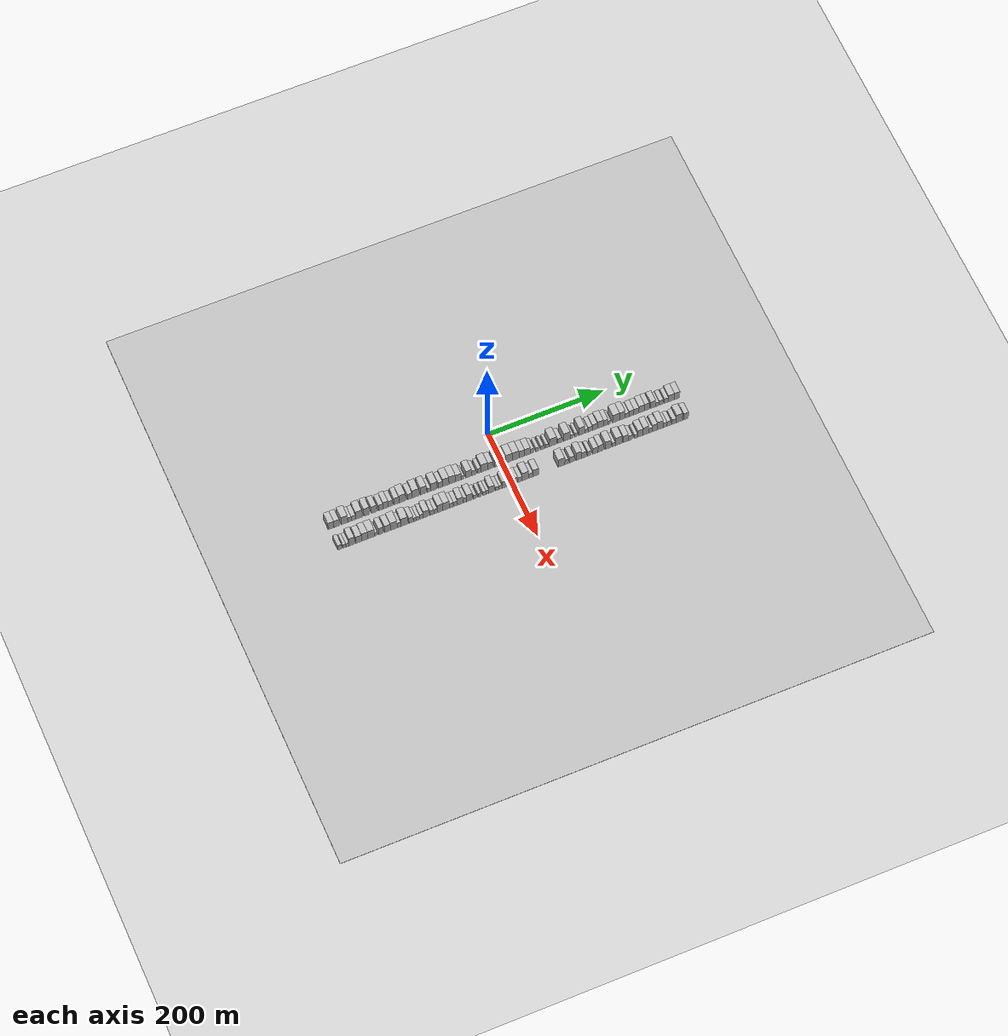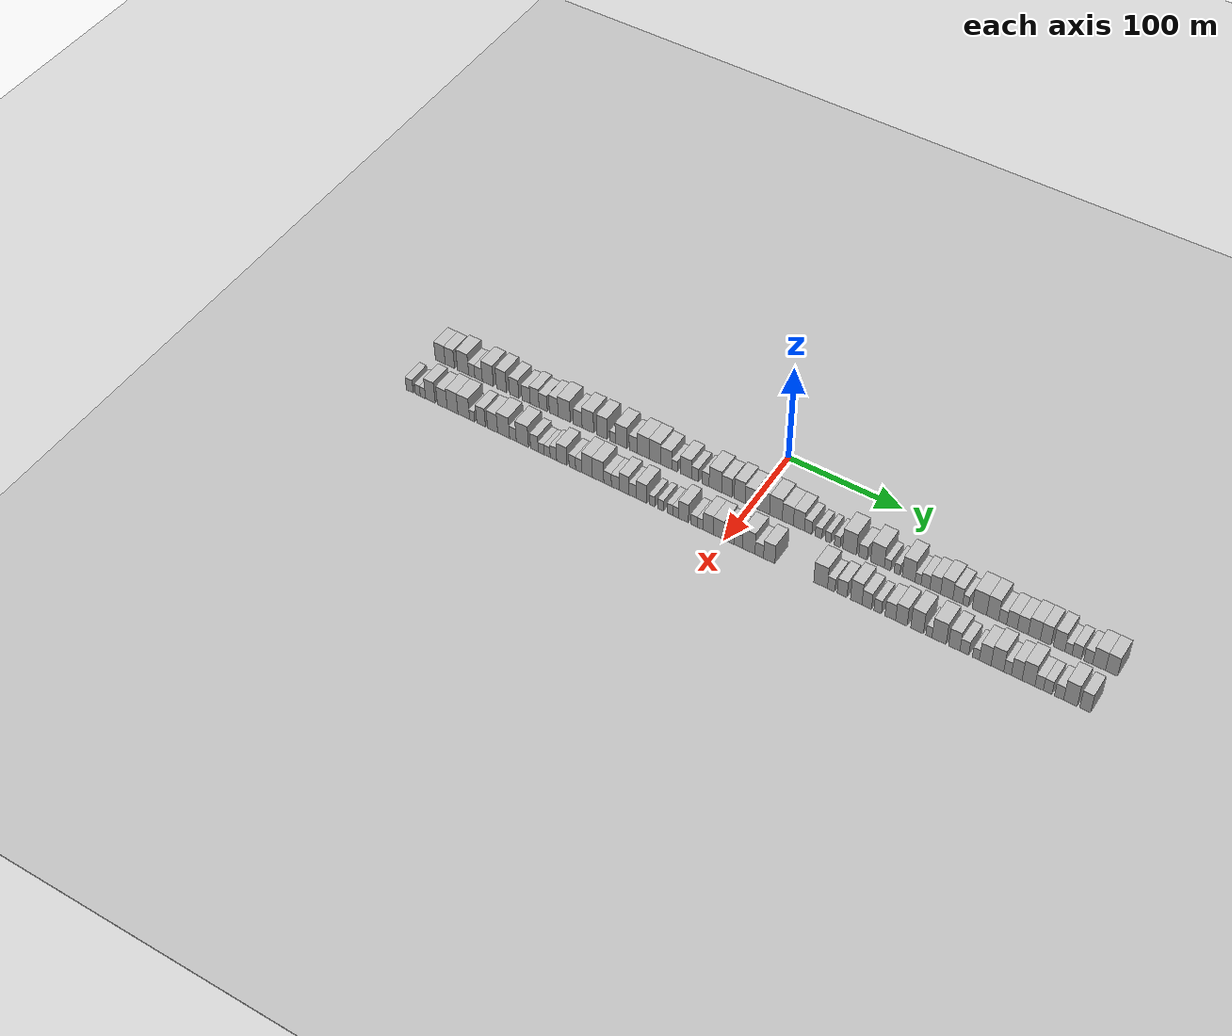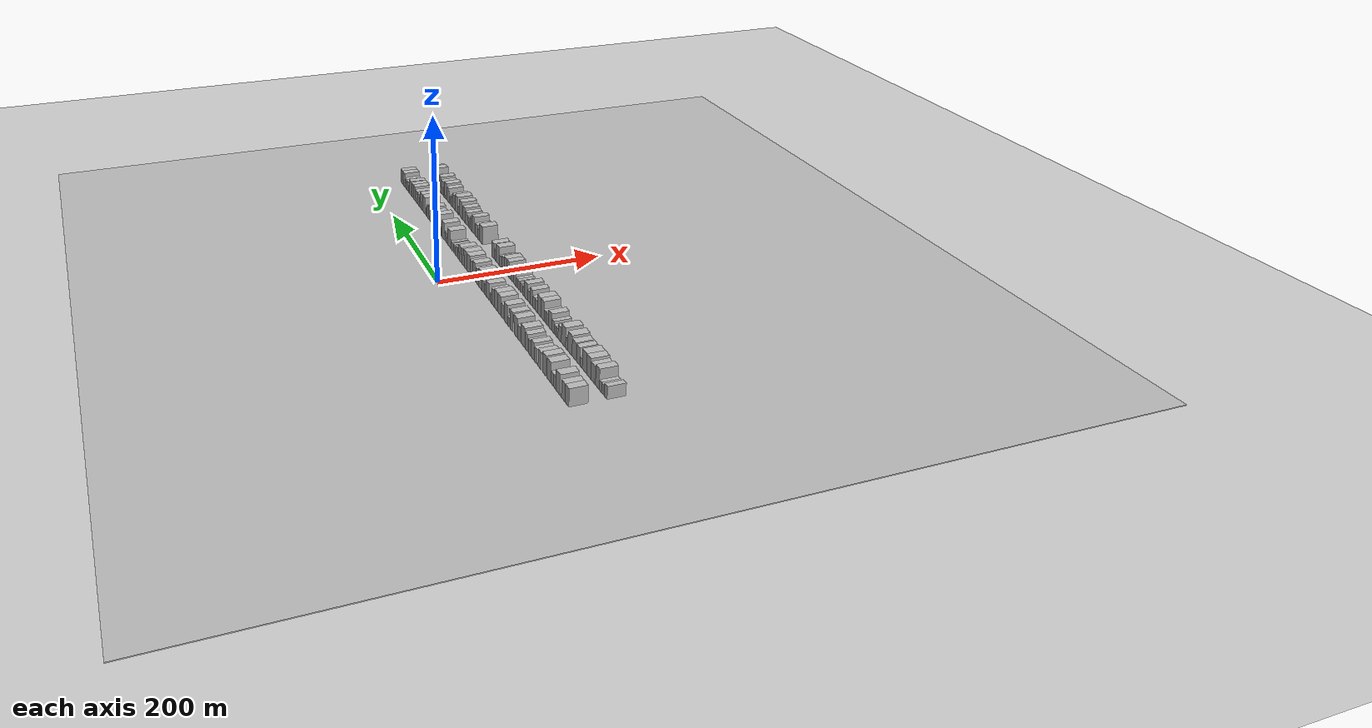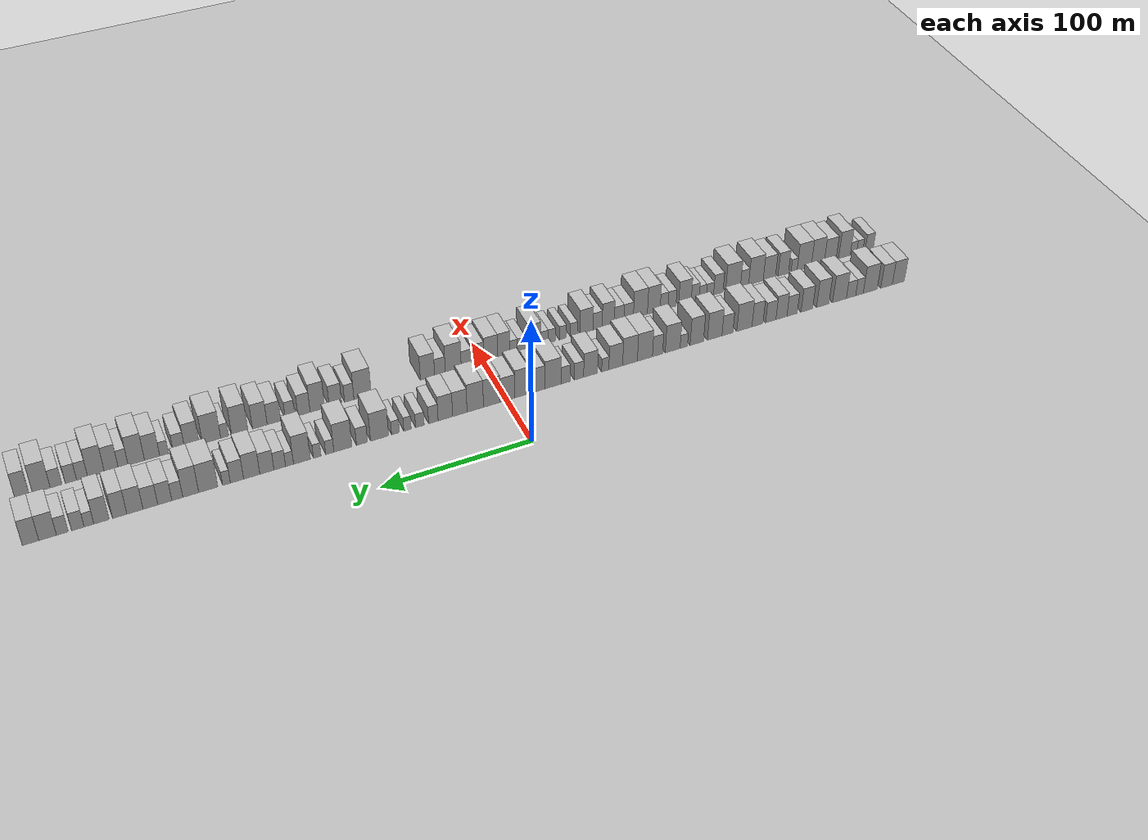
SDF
<?xml version="1.0" encoding="utf-8"?>

<sdf version="1.6">

   <world name="default">

      <gui fullscreen="0">

         <camera name="user_camera">

            <pose>-15 0 4.57585 0 0 0</pose>

            <view_controller>orbit</view_controller>

         </camera>

      </gui>

      <scene>

         <sky>

           <clouds>

             <speed>12</speed>

           </clouds>

         </sky>

         <ambient>0.4 0.4 0.4 1</ambient>

         <background>0.7 0.7 0.7 1</background>

         <shadows>1</shadows>

      </scene>

      <gravity>0 0 -9.8066</gravity>

      <magnetic_field>6e-06 2.3e-05 -4.2e-05</magnetic_field>

      <physics default="0" name="default_physics" type="ode">

         <ode>

            <solver>

               <type>quick</type>

               <iters>10</iters>

               <sor>1.0</sor>

               <use_dynamic_moi_rescaling>0</use_dynamic_moi_rescaling>

            </solver>

            <constraints>

               <cfm>0</cfm>

               <erp>0.2</erp>

               <contact_max_correcting_vel>100</contact_max_correcting_vel>

               <contact_surface_layer>0.001</contact_surface_layer>

            </constraints>

         </ode>

         <max_step_size>0.004</max_step_size>

         <real_time_factor>1</real_time_factor>

         <real_time_update_rate>250</real_time_update_rate>

      </physics>

      <light name="sun" type="directional">

         <cast_shadows>1</cast_shadows>

         <pose>0 0 10 0 0 0</pose>

         <diffuse>0.8 0.8 0.8 1</diffuse>

         <specular>0.2 0.2 0.2 1</specular>

         <attenuation>

            <range>1000</range>

            <constant>0.9</constant>

            <linear>0.01</linear>

            <quadratic>0.001</quadratic>

         </attenuation>

         <direction>-0.5 0.1 -0.9</direction>

      </light>

      <include>

         <name>ground_plane_1</name>

         <uri>model://HANNAS_ground_plane</uri>

         <pose>0 0 0  0 0 0</pose>

      </include>

      <include>

         <name>ground_plane_2</name>

         <uri>model://HANNAS_ground_plane</uri>

         <pose>100 0 0  0 0 0</pose>

      </include>

      <model name="building_1">

         <static>1</static>

         <pose frame="">50.0000 -295.0682 0 0.000000 0.000000 0.000000</pose>

         <link name="link">

            <pose frame="">0 0 10.50 0 0 0</pose>

            <collision name="collision">

               <geometry>

                  <box>

                     <size>20.0000 9.8636 21.0000</size>

                  </box>

               </geometry>

               <max_contacts>10</max_contacts>

               <surface>

                  <contact>

                     <ode/>

                  </contact>

                  <bounce/>

                  <friction>

                     <torsional>

                        <ode/>

                     </torsional>

                     <ode/>

                  </friction>

               </surface>

            </collision>

            <visual name="visual">

               <cast_shadows>0</cast_shadows>

               <geometry>

                  <box>

                     <size>20.0000 9.8636 21.0000</size>

                  </box>

               </geometry>

               <material>

                  <script>

                     <uri>model://HANNAS_wall/materials/scripts</uri>

                     <uri>model://HANNAS_wall/materials/textures</uri>

                     <name>vrc/HANNAS_wall</name>

                  </script>

               </material>

            </visual>

            <self_collide>0</self_collide>

            <enable_wind>0</enable_wind>

            <kinematic>0</kinematic>

         </link>

      </model>

      <model name="building_2">

         <static>1</static>

         <pose frame="">50.0000 -285.4610 0 0.000000 0.000000 0.000000</pose>

         <link name="link">

            <pose frame="">0 0 10.50 0 0 0</pose>

            <collision name="collision">

               <geometry>

                  <box>

                     <size>20.0000 9.3509 21.0000</size>

                  </box>

               </geometry>

               <max_contacts>10</max_contacts>

               <surface>

                  <contact>

                     <ode/>

                  </contact>

                  <bounce/>

                  <friction>

                     <torsional>

                        <ode/>

                     </torsional>

                     <ode/>

                  </friction>

               </surface>

            </collision>

            <visual name="visual">

               <cast_shadows>0</cast_shadows>

               <geometry>

                  <box>

                     <size>20.0000 9.3509 21.0000</size>

                  </box>

               </geometry>

               <material>

                  <script>

                     <uri>model://HANNAS_wall/materials/scripts</uri>

                     <uri>model://HANNAS_wall/materials/textures</uri>

                     <name>vrc/HANNAS_wall</name>

                  </script>

               </material>

            </visual>

            <self_collide>0</self_collide>

            <enable_wind>0</enable_wind>

            <kinematic>0</kinematic>

         </link>

      </model>

      <model name="building_3">

         <static>1</static>

         <pose frame="">50.0000 -272.1908 0 0.000000 0.000000 0.000000</pose>

         <link name="link">

            <pose frame="">0 0 12.00 0 0 0</pose>

            <collision name="collision">

               <geometry>

                  <box>

                     <size>20.0000 11.1894 24.0000</size>

                  </box>

               </geometry>

               <max_contacts>10</max_contacts>

               <surface>

                  <contact>

                     <ode/>

                  </contact>

                  <bounce/>

                  <friction>

                     <torsional>

                        <ode/>

                     </torsional>

                     <ode/>

                  </friction>

               </surface>

            </collision>

            <visual name="visual">

               <cast_shadows>0</cast_shadows>

               <geometry>

                  <box>

                     <size>20.0000 11.1894 24.0000</size>

                  </box>

               </geometry>

               <material>

                  <script>

                     <uri>model://HANNAS_wall/materials/scripts</uri>

                     <uri>model://HANNAS_wall/materials/textures</uri>

                     <name>vrc/HANNAS_wall</name>

                  </script>

               </material>

            </visual>

            <self_collide>0</self_collide>

            <enable_wind>0</enable_wind>

            <kinematic>0</kinematic>

         </link>

      </model>

      <model name="building_4">

         <static>1</static>

         <pose frame="">50.0000 -263.5860 0 0.000000 0.000000 0.000000</pose>

         <link name="link">

            <pose frame="">0 0 7.50 0 0 0</pose>

            <collision name="collision">

               <geometry>

                  <box>

                     <size>20.0000 6.0203 15.0000</size>

                  </box>

               </geometry>

               <max_contacts>10</max_contacts>

               <surface>

                  <contact>

                     <ode/>

                  </contact>

                  <bounce/>

                  <friction>

                     <torsional>

                        <ode/>

                     </torsional>

                     <ode/>

                  </friction>

               </surface>

            </collision>

            <visual name="visual">

               <cast_shadows>0</cast_shadows>

               <geometry>

                  <box>

                     <size>20.0000 6.0203 15.0000</size>

                  </box>

               </geometry>

               <material>

                  <script>

                     <uri>model://HANNAS_wall/materials/scripts</uri>

                     <uri>model://HANNAS_wall/materials/textures</uri>

                     <name>vrc/HANNAS_wall</name>

                  </script>

               </material>

            </visual>

            <self_collide>0</self_collide>

            <enable_wind>0</enable_wind>

            <kinematic>0</kinematic>

         </link>

      </model>

      <model name="building_5">

         <static>1</static>

         <pose frame="">50.0000 -256.8483 0 0.000000 0.000000 0.000000</pose>

         <link name="link">

            <pose frame="">0 0 7.50 0 0 0</pose>

            <collision name="collision">

               <geometry>

                  <box>

                     <size>20.0000 7.4551 15.0000</size>

                  </box>

               </geometry>

               <max_contacts>10</max_contacts>

               <surface>

                  <contact>

                     <ode/>

                  </contact>

                  <bounce/>

                  <friction>

                     <torsional>

                        <ode/>

                     </torsional>

                     <ode/>

                  </friction>

               </surface>

            </collision>

            <visual name="visual">

               <cast_shadows>0</cast_shadows>

               <geometry>

                  <box>

                     <size>20.0000 7.4551 15.0000</size>

                  </box>

               </geometry>

               <material>

                  <script>

                     <uri>model://HANNAS_wall/materials/scripts</uri>

                     <uri>model://HANNAS_wall/materials/textures</uri>

                     <name>vrc/HANNAS_wall</name>

                  </script>

               </material>

            </visual>

            <self_collide>0</self_collide>

            <enable_wind>0</enable_wind>

            <kinematic>0</kinematic>

         </link>

      </model>

      <model name="building_6">

         <static>1</static>

         <pose frame="">50.0000 -247.6045 0 0.000000 0.000000 0.000000</pose>

         <link name="link">

            <pose frame="">0 0 12.00 0 0 0</pose>

            <collision name="collision">

               <geometry>

                  <box>

                     <size>20.0000 11.0326 24.0000</size>

                  </box>

               </geometry>

               <max_contacts>10</max_contacts>

               <surface>

                  <contact>

                     <ode/>

                  </contact>

                  <bounce/>

                  <friction>

                     <torsional>

                        <ode/>

                     </torsional>

                     <ode/>

                  </friction>

               </surface>

            </collision>

            <visual name="visual">

               <cast_shadows>0</cast_shadows>

               <geometry>

                  <box>

                     <size>20.0000 11.0326 24.0000</size>

                  </box>

               </geometry>

               <material>

                  <script>

                     <uri>model://HANNAS_wall/materials/scripts</uri>

                     <uri>model://HANNAS_wall/materials/textures</uri>

                     <name>vrc/HANNAS_wall</name>

                  </script>

               </material>

            </visual>

            <self_collide>0</self_collide>

            <enable_wind>0</enable_wind>

            <kinematic>0</kinematic>

         </link>

      </model>

      <model name="building_7">

         <static>1</static>

         <pose frame="">50.0000 -234.2072 0 0.000000 0.000000 0.000000</pose>

         <link name="link">

            <pose frame="">0 0 12.00 0 0 0</pose>

            <collision name="collision">

               <geometry>

                  <box>

                     <size>20.0000 9.7619 24.0000</size>

                  </box>

               </geometry>

               <max_contacts>10</max_contacts>

               <surface>

                  <contact>

                     <ode/>

                  </contact>

                  <bounce/>

                  <friction>

                     <torsional>

                        <ode/>

                     </torsional>

                     <ode/>

                  </friction>

               </surface>

            </collision>

            <visual name="visual">

               <cast_shadows>0</cast_shadows>

               <geometry>

                  <box>

                     <size>20.0000 9.7619 24.0000</size>

                  </box>

               </geometry>

               <material>

                  <script>

                     <uri>model://HANNAS_wall/materials/scripts</uri>

                     <uri>model://HANNAS_wall/materials/textures</uri>

                     <name>vrc/HANNAS_wall</name>

                  </script>

               </material>

            </visual>

            <self_collide>0</self_collide>

            <enable_wind>0</enable_wind>

            <kinematic>0</kinematic>

         </link>

      </model>

      <model name="building_8">

         <static>1</static>

         <pose frame="">50.0000 -221.7563 0 0.000000 0.000000 0.000000</pose>

         <link name="link">

            <pose frame="">0 0 10.50 0 0 0</pose>

            <collision name="collision">

               <geometry>

                  <box>

                     <size>20.0000 9.1400 21.0000</size>

                  </box>

               </geometry>

               <max_contacts>10</max_contacts>

               <surface>

                  <contact>

                     <ode/>

                  </contact>

                  <bounce/>

                  <friction>

                     <torsional>

                        <ode/>

                     </torsional>

                     <ode/>

                  </friction>

               </surface>

            </collision>

            <visual name="visual">

               <cast_shadows>0</cast_shadows>

               <geometry>

                  <box>

                     <size>20.0000 9.1400 21.0000</size>

                  </box>

               </geometry>

               <material>

                  <script>

                     <uri>model://HANNAS_wall/materials/scripts</uri>

                     <uri>model://HANNAS_wall/materials/textures</uri>

                     <name>vrc/HANNAS_wall</name>

                  </script>

               </material>

            </visual>

            <self_collide>0</self_collide>

            <enable_wind>0</enable_wind>

            <kinematic>0</kinematic>

         </link>

      </model>

      <model name="building_9">

         <static>1</static>

         <pose frame="">50.0000 -210.1605 0 0.000000 0.000000 0.000000</pose>

         <link name="link">

            <pose frame="">0 0 9.00 0 0 0</pose>

            <collision name="collision">

               <geometry>

                  <box>

                     <size>20.0000 8.0516 18.0000</size>

                  </box>

               </geometry>

               <max_contacts>10</max_contacts>

               <surface>

                  <contact>

                     <ode/>

                  </contact>

                  <bounce/>

                  <friction>

                     <torsional>

                        <ode/>

                     </torsional>

                     <ode/>

                  </friction>

               </surface>

            </collision>

            <visual name="visual">

               <cast_shadows>0</cast_shadows>

               <geometry>

                  <box>

                     <size>20.0000 8.0516 18.0000</size>

                  </box>

               </geometry>

               <material>

                  <script>

                     <uri>model://HANNAS_wall/materials/scripts</uri>

                     <uri>model://HANNAS_wall/materials/textures</uri>

                     <name>vrc/HANNAS_wall</name>

                  </script>

               </material>

            </visual>

            <self_collide>0</self_collide>

            <enable_wind>0</enable_wind>

            <kinematic>0</kinematic>

         </link>

      </model>

      <model name="building_10">

         <static>1</static>

         <pose frame="">50.0000 -201.8619 0 0.000000 0.000000 0.000000</pose>

         <link name="link">

            <pose frame="">0 0 10.50 0 0 0</pose>

            <collision name="collision">

               <geometry>

                  <box>

                     <size>20.0000 8.5455 21.0000</size>

                  </box>

               </geometry>

               <max_contacts>10</max_contacts>

               <surface>

                  <contact>

                     <ode/>

                  </contact>

                  <bounce/>

                  <friction>

                     <torsional>

                        <ode/>

                     </torsional>

                     <ode/>

                  </friction>

               </surface>

            </collision>

            <visual name="visual">

               <cast_shadows>0</cast_shadows>

               <geometry>

                  <box>

                     <size>20.0000 8.5455 21.0000</size>

                  </box>

               </geometry>

               <material>

                  <script>

                     <uri>model://HANNAS_wall/materials/scripts</uri>

                     <uri>model://HANNAS_wall/materials/textures</uri>

                     <name>vrc/HANNAS_wall</name>

                  </script>

               </material>

            </visual>

            <self_collide>0</self_collide>

            <enable_wind>0</enable_wind>

            <kinematic>0</kinematic>

         </link>

      </model>

      <model name="building_11">

         <static>1</static>

         <pose frame="">50.0000 -193.5754 0 0.000000 0.000000 0.000000</pose>

         <link name="link">

            <pose frame="">0 0 9.00 0 0 0</pose>

            <collision name="collision">

               <geometry>

                  <box>

                     <size>20.0000 8.0274 18.0000</size>

                  </box>

               </geometry>

               <max_contacts>10</max_contacts>

               <surface>

                  <contact>

                     <ode/>

                  </contact>

                  <bounce/>

                  <friction>

                     <torsional>

                        <ode/>

                     </torsional>

                     <ode/>

                  </friction>

               </surface>

            </collision>

            <visual name="visual">

               <cast_shadows>0</cast_shadows>

               <geometry>

                  <box>

                     <size>20.0000 8.0274 18.0000</size>

                  </box>

               </geometry>

               <material>

                  <script>

                     <uri>model://HANNAS_wall/materials/scripts</uri>

                     <uri>model://HANNAS_wall/materials/textures</uri>

                     <name>vrc/HANNAS_wall</name>

                  </script>

               </material>

            </visual>

            <self_collide>0</self_collide>

            <enable_wind>0</enable_wind>

            <kinematic>0</kinematic>

         </link>

      </model>

      <model name="building_12">

         <static>1</static>

         <pose frame="">50.0000 -183.3138 0 0.000000 0.000000 0.000000</pose>

         <link name="link">

            <pose frame="">0 0 10.50 0 0 0</pose>

            <collision name="collision">

               <geometry>

                  <box>

                     <size>20.0000 8.4959 21.0000</size>

                  </box>

               </geometry>

               <max_contacts>10</max_contacts>

               <surface>

                  <contact>

                     <ode/>

                  </contact>

                  <bounce/>

                  <friction>

                     <torsional>

                        <ode/>

                     </torsional>

                     <ode/>

                  </friction>

               </surface>

            </collision>

            <visual name="visual">

               <cast_shadows>0</cast_shadows>

               <geometry>

                  <box>

                     <size>20.0000 8.4959 21.0000</size>

                  </box>

               </geometry>

               <material>

                  <script>

                     <uri>model://HANNAS_wall/materials/scripts</uri>

                     <uri>model://HANNAS_wall/materials/textures</uri>

                     <name>vrc/HANNAS_wall</name>

                  </script>

               </material>

            </visual>

            <self_collide>0</self_collide>

            <enable_wind>0</enable_wind>

            <kinematic>0</kinematic>

         </link>

      </model>

      <model name="building_13">

         <static>1</static>

         <pose frame="">50.0000 -173.2645 0 0.000000 0.000000 0.000000</pose>

         <link name="link">

            <pose frame="">0 0 12.00 0 0 0</pose>

            <collision name="collision">

               <geometry>

                  <box>

                     <size>20.0000 11.6026 24.0000</size>

                  </box>

               </geometry>

               <max_contacts>10</max_contacts>

               <surface>

                  <contact>

                     <ode/>

                  </contact>

                  <bounce/>

                  <friction>

                     <torsional>

                        <ode/>

                     </torsional>

                     <ode/>

                  </friction>

               </surface>

            </collision>

            <visual name="visual">

               <cast_shadows>0</cast_shadows>

               <geometry>

                  <box>

                     <size>20.0000 11.6026 24.0000</size>

                  </box>

               </geometry>

               <material>

                  <script>

                     <uri>model://HANNAS_wall/materials/scripts</uri>

                     <uri>model://HANNAS_wall/materials/textures</uri>

                     <name>vrc/HANNAS_wall</name>

                  </script>

               </material>

            </visual>

            <self_collide>0</self_collide>

            <enable_wind>0</enable_wind>

            <kinematic>0</kinematic>

         </link>

      </model>

      <model name="building_14">

         <static>1</static>

         <pose frame="">50.0000 -160.3290 0 0.000000 0.000000 0.000000</pose>

         <link name="link">

            <pose frame="">0 0 9.00 0 0 0</pose>

            <collision name="collision">

               <geometry>

                  <box>

                     <size>20.0000 8.2686 18.0000</size>

                  </box>

               </geometry>

               <max_contacts>10</max_contacts>

               <surface>

                  <contact>

                     <ode/>

                  </contact>

                  <bounce/>

                  <friction>

                     <torsional>

                        <ode/>

                     </torsional>

                     <ode/>

                  </friction>

               </surface>

            </collision>

            <visual name="visual">

               <cast_shadows>0</cast_shadows>

               <geometry>

                  <box>

                     <size>20.0000 8.2686 18.0000</size>

                  </box>

               </geometry>

               <material>

                  <script>

                     <uri>model://HANNAS_wall/materials/scripts</uri>

                     <uri>model://HANNAS_wall/materials/textures</uri>

                     <name>vrc/HANNAS_wall</name>

                  </script>

               </material>

            </visual>

            <self_collide>0</self_collide>

            <enable_wind>0</enable_wind>

            <kinematic>0</kinematic>

         </link>

      </model>

      <model name="building_15">

         <static>1</static>

         <pose frame="">50.0000 -150.6718 0 0.000000 0.000000 0.000000</pose>

         <link name="link">

            <pose frame="">0 0 12.00 0 0 0</pose>

            <collision name="collision">

               <geometry>

                  <box>

                     <size>20.0000 11.0457 24.0000</size>

                  </box>

               </geometry>

               <max_contacts>10</max_contacts>

               <surface>

                  <contact>

                     <ode/>

                  </contact>

                  <bounce/>

                  <friction>

                     <torsional>

                        <ode/>

                     </torsional>

                     <ode/>

                  </friction>

               </surface>

            </collision>

            <visual name="visual">

               <cast_shadows>0</cast_shadows>

               <geometry>

                  <box>

                     <size>20.0000 11.0457 24.0000</size>

                  </box>

               </geometry>

               <material>

                  <script>

                     <uri>model://HANNAS_wall/materials/scripts</uri>

                     <uri>model://HANNAS_wall/materials/textures</uri>

                     <name>vrc/HANNAS_wall</name>

                  </script>

               </material>

            </visual>

            <self_collide>0</self_collide>

            <enable_wind>0</enable_wind>

            <kinematic>0</kinematic>

         </link>

      </model>

      <model name="building_16">

         <static>1</static>

         <pose frame="">50.0000 -137.1305 0 0.000000 0.000000 0.000000</pose>

         <link name="link">

            <pose frame="">0 0 12.00 0 0 0</pose>

            <collision name="collision">

               <geometry>

                  <box>

                     <size>20.0000 10.0370 24.0000</size>

                  </box>

               </geometry>

               <max_contacts>10</max_contacts>

               <surface>

                  <contact>

                     <ode/>

                  </contact>

                  <bounce/>

                  <friction>

                     <torsional>

                        <ode/>

                     </torsional>

                     <ode/>

                  </friction>

               </surface>

            </collision>

            <visual name="visual">

               <cast_shadows>0</cast_shadows>

               <geometry>

                  <box>

                     <size>20.0000 10.0370 24.0000</size>

                  </box>

               </geometry>

               <material>

                  <script>

                     <uri>model://HANNAS_wall/materials/scripts</uri>

                     <uri>model://HANNAS_wall/materials/textures</uri>

                     <name>vrc/HANNAS_wall</name>

                  </script>

               </material>

            </visual>

            <self_collide>0</self_collide>

            <enable_wind>0</enable_wind>

            <kinematic>0</kinematic>

         </link>

      </model>

      <model name="building_17">

         <static>1</static>

         <pose frame="">50.0000 -127.3615 0 0.000000 0.000000 0.000000</pose>

         <link name="link">

            <pose frame="">0 0 6.00 0 0 0</pose>

            <collision name="collision">

               <geometry>

                  <box>

                     <size>20.0000 5.5009 12.0000</size>

                  </box>

               </geometry>

               <max_contacts>10</max_contacts>

               <surface>

                  <contact>

                     <ode/>

                  </contact>

                  <bounce/>

                  <friction>

                     <torsional>

                        <ode/>

                     </torsional>

                     <ode/>

                  </friction>

               </surface>

            </collision>

            <visual name="visual">

               <cast_shadows>0</cast_shadows>

               <geometry>

                  <box>

                     <size>20.0000 5.5009 12.0000</size>

                  </box>

               </geometry>

               <material>

                  <script>

                     <uri>model://HANNAS_wall/materials/scripts</uri>

                     <uri>model://HANNAS_wall/materials/textures</uri>

                     <name>vrc/HANNAS_wall</name>

                  </script>

               </material>

            </visual>

            <self_collide>0</self_collide>

            <enable_wind>0</enable_wind>

            <kinematic>0</kinematic>

         </link>

      </model>

      <model name="building_18">

         <static>1</static>

         <pose frame="">50.0000 -119.1126 0 0.000000 0.000000 0.000000</pose>

         <link name="link">

            <pose frame="">0 0 12.00 0 0 0</pose>

            <collision name="collision">

               <geometry>

                  <box>

                     <size>20.0000 10.9968 24.0000</size>

                  </box>

               </geometry>

               <max_contacts>10</max_contacts>

               <surface>

                  <contact>

                     <ode/>

                  </contact>

                  <bounce/>

                  <friction>

                     <torsional>

                        <ode/>

                     </torsional>

                     <ode/>

                  </friction>

               </surface>

            </collision>

            <visual name="visual">

               <cast_shadows>0</cast_shadows>

               <geometry>

                  <box>

                     <size>20.0000 10.9968 24.0000</size>

                  </box>

               </geometry>

               <material>

                  <script>

                     <uri>model://HANNAS_wall/materials/scripts</uri>

                     <uri>model://HANNAS_wall/materials/textures</uri>

                     <name>vrc/HANNAS_wall</name>

                  </script>

               </material>

            </visual>

            <self_collide>0</self_collide>

            <enable_wind>0</enable_wind>

            <kinematic>0</kinematic>

         </link>

      </model>

      <model name="building_19">

         <static>1</static>

         <pose frame="">50.0000 -107.8722 0 0.000000 0.000000 0.000000</pose>

         <link name="link">

            <pose frame="">0 0 9.00 0 0 0</pose>

            <collision name="collision">

               <geometry>

                  <box>

                     <size>20.0000 7.4841 18.0000</size>

                  </box>

               </geometry>

               <max_contacts>10</max_contacts>

               <surface>

                  <contact>

                     <ode/>

                  </contact>

                  <bounce/>

                  <friction>

                     <torsional>

                        <ode/>

                     </torsional>

                     <ode/>

                  </friction>

               </surface>

            </collision>

            <visual name="visual">

               <cast_shadows>0</cast_shadows>

               <geometry>

                  <box>

                     <size>20.0000 7.4841 18.0000</size>

                  </box>

               </geometry>

               <material>

                  <script>

                     <uri>model://HANNAS_wall/materials/scripts</uri>

                     <uri>model://HANNAS_wall/materials/textures</uri>

                     <name>vrc/HANNAS_wall</name>

                  </script>

               </material>

            </visual>

            <self_collide>0</self_collide>

            <enable_wind>0</enable_wind>

            <kinematic>0</kinematic>

         </link>

      </model>

      <model name="building_20">

         <static>1</static>

         <pose frame="">50.0000 -98.5903 0 0.000000 0.000000 0.000000</pose>

         <link name="link">

            <pose frame="">0 0 12.00 0 0 0</pose>

            <collision name="collision">

               <geometry>

                  <box>

                     <size>20.0000 11.0796 24.0000</size>

                  </box>

               </geometry>

               <max_contacts>10</max_contacts>

               <surface>

                  <contact>

                     <ode/>

                  </contact>

                  <bounce/>

                  <friction>

                     <torsional>

                        <ode/>

                     </torsional>

                     <ode/>

                  </friction>

               </surface>

            </collision>

            <visual name="visual">

               <cast_shadows>0</cast_shadows>

               <geometry>

                  <box>

                     <size>20.0000 11.0796 24.0000</size>

                  </box>

               </geometry>

               <material>

                  <script>

                     <uri>model://HANNAS_wall/materials/scripts</uri>

                     <uri>model://HANNAS_wall/materials/textures</uri>

                     <name>vrc/HANNAS_wall</name>

                  </script>

               </material>

            </visual>

            <self_collide>0</self_collide>

            <enable_wind>0</enable_wind>

            <kinematic>0</kinematic>

         </link>

      </model>

      <model name="building_21">

         <static>1</static>

         <pose frame="">50.0000 -87.6464 0 0.000000 0.000000 0.000000</pose>

         <link name="link">

            <pose frame="">0 0 12.00 0 0 0</pose>

            <collision name="collision">

               <geometry>

                  <box>

                     <size>20.0000 10.8083 24.0000</size>

                  </box>

               </geometry>

               <max_contacts>10</max_contacts>

               <surface>

                  <contact>

                     <ode/>

                  </contact>

                  <bounce/>

                  <friction>

                     <torsional>

                        <ode/>

                     </torsional>

                     <ode/>

                  </friction>

               </surface>

            </collision>

            <visual name="visual">

               <cast_shadows>0</cast_shadows>

               <geometry>

                  <box>

                     <size>20.0000 10.8083 24.0000</size>

                  </box>

               </geometry>

               <material>

                  <script>

                     <uri>model://HANNAS_wall/materials/scripts</uri>

                     <uri>model://HANNAS_wall/materials/textures</uri>

                     <name>vrc/HANNAS_wall</name>

                  </script>

               </material>

            </visual>

            <self_collide>0</self_collide>

            <enable_wind>0</enable_wind>

            <kinematic>0</kinematic>

         </link>

      </model>

      <model name="building_22">

         <static>1</static>

         <pose frame="">50.0000 -77.2396 0 0.000000 0.000000 0.000000</pose>

         <link name="link">

            <pose frame="">0 0 10.50 0 0 0</pose>

            <collision name="collision">

               <geometry>

                  <box>

                     <size>20.0000 10.0054 21.0000</size>

                  </box>

               </geometry>

               <max_contacts>10</max_contacts>

               <surface>

                  <contact>

                     <ode/>

                  </contact>

                  <bounce/>

                  <friction>

                     <torsional>

                        <ode/>

                     </torsional>

                     <ode/>

                  </friction>

               </surface>

            </collision>

            <visual name="visual">

               <cast_shadows>0</cast_shadows>

               <geometry>

                  <box>

                     <size>20.0000 10.0054 21.0000</size>

                  </box>

               </geometry>

               <material>

                  <script>

                     <uri>model://HANNAS_wall/materials/scripts</uri>

                     <uri>model://HANNAS_wall/materials/textures</uri>

                     <name>vrc/HANNAS_wall</name>

                  </script>

               </material>

            </visual>

            <self_collide>0</self_collide>

            <enable_wind>0</enable_wind>

            <kinematic>0</kinematic>

         </link>

      </model>

      <model name="building_23">

         <static>1</static>

         <pose frame="">50.0000 -69.6298 0 0.000000 0.000000 0.000000</pose>

         <link name="link">

            <pose frame="">0 0 6.00 0 0 0</pose>

            <collision name="collision">

               <geometry>

                  <box>

                     <size>20.0000 5.2142 12.0000</size>

                  </box>

               </geometry>

               <max_contacts>10</max_contacts>

               <surface>

                  <contact>

                     <ode/>

                  </contact>

                  <bounce/>

                  <friction>

                     <torsional>

                        <ode/>

                     </torsional>

                     <ode/>

                  </friction>

               </surface>

            </collision>

            <visual name="visual">

               <cast_shadows>0</cast_shadows>

               <geometry>

                  <box>

                     <size>20.0000 5.2142 12.0000</size>

                  </box>

               </geometry>

               <material>

                  <script>

                     <uri>model://HANNAS_wall/materials/scripts</uri>

                     <uri>model://HANNAS_wall/materials/textures</uri>

                     <name>vrc/HANNAS_wall</name>

                  </script>

               </material>

            </visual>

            <self_collide>0</self_collide>

            <enable_wind>0</enable_wind>

            <kinematic>0</kinematic>

         </link>

      </model>

      <model name="building_24">

         <static>1</static>

         <pose frame="">50.0000 -59.0268 0 0.000000 0.000000 0.000000</pose>

         <link name="link">

            <pose frame="">0 0 10.50 0 0 0</pose>

            <collision name="collision">

               <geometry>

                  <box>

                     <size>20.0000 9.9916 21.0000</size>

                  </box>

               </geometry>

               <max_contacts>10</max_contacts>

               <surface>

                  <contact>

                     <ode/>

                  </contact>

                  <bounce/>

                  <friction>

                     <torsional>

                        <ode/>

                     </torsional>

                     <ode/>

                  </friction>

               </surface>

            </collision>

            <visual name="visual">

               <cast_shadows>0</cast_shadows>

               <geometry>

                  <box>

                     <size>20.0000 9.9916 21.0000</size>

                  </box>

               </geometry>

               <material>

                  <script>

                     <uri>model://HANNAS_wall/materials/scripts</uri>

                     <uri>model://HANNAS_wall/materials/textures</uri>

                     <name>vrc/HANNAS_wall</name>

                  </script>

               </material>

            </visual>

            <self_collide>0</self_collide>

            <enable_wind>0</enable_wind>

            <kinematic>0</kinematic>

         </link>

      </model>

      <model name="building_25">

         <static>1</static>

         <pose frame="">50.0000 -50.7129 0 0.000000 0.000000 0.000000</pose>

         <link name="link">

            <pose frame="">0 0 7.50 0 0 0</pose>

            <collision name="collision">

               <geometry>

                  <box>

                     <size>20.0000 6.6363 15.0000</size>

                  </box>

               </geometry>

               <max_contacts>10</max_contacts>

               <surface>

                  <contact>

                     <ode/>

                  </contact>

                  <bounce/>

                  <friction>

                     <torsional>

                        <ode/>

                     </torsional>

                     <ode/>

                  </friction>

               </surface>

            </collision>

            <visual name="visual">

               <cast_shadows>0</cast_shadows>

               <geometry>

                  <box>

                     <size>20.0000 6.6363 15.0000</size>

                  </box>

               </geometry>

               <material>

                  <script>

                     <uri>model://HANNAS_wall/materials/scripts</uri>

                     <uri>model://HANNAS_wall/materials/textures</uri>

                     <name>vrc/HANNAS_wall</name>

                  </script>

               </material>

            </visual>

            <self_collide>0</self_collide>

            <enable_wind>0</enable_wind>

            <kinematic>0</kinematic>

         </link>

      </model>

      <model name="building_26">

         <static>1</static>

         <pose frame="">50.0000 -41.1723 0 0.000000 0.000000 0.000000</pose>

         <link name="link">

            <pose frame="">0 0 7.50 0 0 0</pose>

            <collision name="collision">

               <geometry>

                  <box>

                     <size>20.0000 6.4449 15.0000</size>

                  </box>

               </geometry>

               <max_contacts>10</max_contacts>

               <surface>

                  <contact>

                     <ode/>

                  </contact>

                  <bounce/>

                  <friction>

                     <torsional>

                        <ode/>

                     </torsional>

                     <ode/>

                  </friction>

               </surface>

            </collision>

            <visual name="visual">

               <cast_shadows>0</cast_shadows>

               <geometry>

                  <box>

                     <size>20.0000 6.4449 15.0000</size>

                  </box>

               </geometry>

               <material>

                  <script>

                     <uri>model://HANNAS_wall/materials/scripts</uri>

                     <uri>model://HANNAS_wall/materials/textures</uri>

                     <name>vrc/HANNAS_wall</name>

                  </script>

               </material>

            </visual>

            <self_collide>0</self_collide>

            <enable_wind>0</enable_wind>

            <kinematic>0</kinematic>

         </link>

      </model>

      <model name="building_27">

         <static>1</static>

         <pose frame="">50.0000 -32.1390 0 0.000000 0.000000 0.000000</pose>

         <link name="link">

            <pose frame="">0 0 12.00 0 0 0</pose>

            <collision name="collision">

               <geometry>

                  <box>

                     <size>20.0000 11.6217 24.0000</size>

                  </box>

               </geometry>

               <max_contacts>10</max_contacts>

               <surface>

                  <contact>

                     <ode/>

                  </contact>

                  <bounce/>

                  <friction>

                     <torsional>

                        <ode/>

                     </torsional>

                     <ode/>

                  </friction>

               </surface>

            </collision>

            <visual name="visual">

               <cast_shadows>0</cast_shadows>

               <geometry>

                  <box>

                     <size>20.0000 11.6217 24.0000</size>

                  </box>

               </geometry>

               <material>

                  <script>

                     <uri>model://HANNAS_wall/materials/scripts</uri>

                     <uri>model://HANNAS_wall/materials/textures</uri>

                     <name>vrc/HANNAS_wall</name>

                  </script>

               </material>

            </visual>

            <self_collide>0</self_collide>

            <enable_wind>0</enable_wind>

            <kinematic>0</kinematic>

         </link>

      </model>

      <model name="building_28">

         <static>1</static>

         <pose frame="">50.0000 -21.7275 0 0.000000 0.000000 0.000000</pose>

         <link name="link">

            <pose frame="">0 0 10.50 0 0 0</pose>

            <collision name="collision">

               <geometry>

                  <box>

                     <size>20.0000 9.2012 21.0000</size>

                  </box>

               </geometry>

               <max_contacts>10</max_contacts>

               <surface>

                  <contact>

                     <ode/>

                  </contact>

                  <bounce/>

                  <friction>

                     <torsional>

                        <ode/>

                     </torsional>

                     <ode/>

                  </friction>

               </surface>

            </collision>

            <visual name="visual">

               <cast_shadows>0</cast_shadows>

               <geometry>

                  <box>

                     <size>20.0000 9.2012 21.0000</size>

                  </box>

               </geometry>

               <material>

                  <script>

                     <uri>model://HANNAS_wall/materials/scripts</uri>

                     <uri>model://HANNAS_wall/materials/textures</uri>

                     <name>vrc/HANNAS_wall</name>

                  </script>

               </material>

            </visual>

            <self_collide>0</self_collide>

            <enable_wind>0</enable_wind>

            <kinematic>0</kinematic>

         </link>

      </model>

      <model name="building_29">

         <static>1</static>

         <pose frame="">50.0000 -10.2129 0 0.000000 0.000000 0.000000</pose>

         <link name="link">

            <pose frame="">0 0 12.00 0 0 0</pose>

            <collision name="collision">

               <geometry>

                  <box>

                     <size>20.0000 9.8280 24.0000</size>

                  </box>

               </geometry>

               <max_contacts>10</max_contacts>

               <surface>

                  <contact>

                     <ode/>

                  </contact>

                  <bounce/>

                  <friction>

                     <torsional>

                        <ode/>

                     </torsional>

                     <ode/>

                  </friction>

               </surface>

            </collision>

            <visual name="visual">

               <cast_shadows>0</cast_shadows>

               <geometry>

                  <box>

                     <size>20.0000 9.8280 24.0000</size>

                  </box>

               </geometry>

               <material>

                  <script>

                     <uri>model://HANNAS_wall/materials/scripts</uri>

                     <uri>model://HANNAS_wall/materials/textures</uri>

                     <name>vrc/HANNAS_wall</name>

                  </script>

               </material>

            </visual>

            <self_collide>0</self_collide>

            <enable_wind>0</enable_wind>

            <kinematic>0</kinematic>

         </link>

      </model>

      <model name="building_30">

         <static>1</static>

         <pose frame="">50.0000 -0.1729 0 0.000000 0.000000 0.000000</pose>

         <link name="link">

            <pose frame="">0 0 10.50 0 0 0</pose>

            <collision name="collision">

               <geometry>

                  <box>

                     <size>20.0000 10.2520 21.0000</size>

                  </box>

               </geometry>

               <max_contacts>10</max_contacts>

               <surface>

                  <contact>

                     <ode/>

                  </contact>

                  <bounce/>

                  <friction>

                     <torsional>

                        <ode/>

                     </torsional>

                     <ode/>

                  </friction>

               </surface>

            </collision>

            <visual name="visual">

               <cast_shadows>0</cast_shadows>

               <geometry>

                  <box>

                     <size>20.0000 10.2520 21.0000</size>

                  </box>

               </geometry>

               <material>

                  <script>

                     <uri>model://HANNAS_wall/materials/scripts</uri>

                     <uri>model://HANNAS_wall/materials/textures</uri>

                     <name>vrc/HANNAS_wall</name>

                  </script>

               </material>

            </visual>

            <self_collide>0</self_collide>

            <enable_wind>0</enable_wind>

            <kinematic>0</kinematic>

         </link>

      </model>

      <model name="building_31">

         <static>1</static>

         <pose frame="">50.0000 10.7029 0 0.000000 0.000000 0.000000</pose>

         <link name="link">

            <pose frame="">0 0 12.00 0 0 0</pose>

            <collision name="collision">

               <geometry>

                  <box>

                     <size>20.0000 11.4996 24.0000</size>

                  </box>

               </geometry>

               <max_contacts>10</max_contacts>

               <surface>

                  <contact>

                     <ode/>

                  </contact>

                  <bounce/>

                  <friction>

                     <torsional>

                        <ode/>

                     </torsional>

                     <ode/>

                  </friction>

               </surface>

            </collision>

            <visual name="visual">

               <cast_shadows>0</cast_shadows>

               <geometry>

                  <box>

                     <size>20.0000 11.4996 24.0000</size>

                  </box>

               </geometry>

               <material>

                  <script>

                     <uri>model://HANNAS_wall/materials/scripts</uri>

                     <uri>model://HANNAS_wall/materials/textures</uri>

                     <name>vrc/HANNAS_wall</name>

                  </script>

               </material>

            </visual>

            <self_collide>0</self_collide>

            <enable_wind>0</enable_wind>

            <kinematic>0</kinematic>

         </link>

      </model>

      <model name="building_32">

         <static>1</static>

         <pose frame="">50.0000 22.0867 0 0.000000 0.000000 0.000000</pose>

         <link name="link">

            <pose frame="">0 0 12.00 0 0 0</pose>

            <collision name="collision">

               <geometry>

                  <box>

                     <size>20.0000 11.2679 24.0000</size>

                  </box>

               </geometry>

               <max_contacts>10</max_contacts>

               <surface>

                  <contact>

                     <ode/>

                  </contact>

                  <bounce/>

                  <friction>

                     <torsional>

                        <ode/>

                     </torsional>

                     <ode/>

                  </friction>

               </surface>

            </collision>

            <visual name="visual">

               <cast_shadows>0</cast_shadows>

               <geometry>

                  <box>

                     <size>20.0000 11.2679 24.0000</size>

                  </box>

               </geometry>

               <material>

                  <script>

                     <uri>model://HANNAS_wall/materials/scripts</uri>

                     <uri>model://HANNAS_wall/materials/textures</uri>

                     <name>vrc/HANNAS_wall</name>

                  </script>

               </material>

            </visual>

            <self_collide>0</self_collide>

            <enable_wind>0</enable_wind>

            <kinematic>0</kinematic>

         </link>

      </model>

      <model name="building_33">

         <static>1</static>

         <pose frame="">50.0000 32.6490 0 0.000000 0.000000 0.000000</pose>

         <link name="link">

            <pose frame="">0 0 10.50 0 0 0</pose>

            <collision name="collision">

               <geometry>

                  <box>

                     <size>20.0000 9.8569 21.0000</size>

                  </box>

               </geometry>

               <max_contacts>10</max_contacts>

               <surface>

                  <contact>

                     <ode/>

                  </contact>

                  <bounce/>

                  <friction>

                     <torsional>

                        <ode/>

                     </torsional>

                     <ode/>

                  </friction>

               </surface>

            </collision>

            <visual name="visual">

               <cast_shadows>0</cast_shadows>

               <geometry>

                  <box>

                     <size>20.0000 9.8569 21.0000</size>

                  </box>

               </geometry>

               <material>

                  <script>

                     <uri>model://HANNAS_wall/materials/scripts</uri>

                     <uri>model://HANNAS_wall/materials/textures</uri>

                     <name>vrc/HANNAS_wall</name>

                  </script>

               </material>

            </visual>

            <self_collide>0</self_collide>

            <enable_wind>0</enable_wind>

            <kinematic>0</kinematic>

         </link>

      </model>

      <model name="building_34">

         <static>1</static>

         <pose frame="">50.0000 42.4987 0 0.000000 0.000000 0.000000</pose>

         <link name="link">

            <pose frame="">0 0 10.50 0 0 0</pose>

            <collision name="collision">

               <geometry>

                  <box>

                     <size>20.0000 9.8425 21.0000</size>

                  </box>

               </geometry>

               <max_contacts>10</max_contacts>

               <surface>

                  <contact>

                     <ode/>

                  </contact>

                  <bounce/>

                  <friction>

                     <torsional>

                        <ode/>

                     </torsional>

                     <ode/>

                  </friction>

               </surface>

            </collision>

            <visual name="visual">

               <cast_shadows>0</cast_shadows>

               <geometry>

                  <box>

                     <size>20.0000 9.8425 21.0000</size>

                  </box>

               </geometry>

               <material>

                  <script>

                     <uri>model://HANNAS_wall/materials/scripts</uri>

                     <uri>model://HANNAS_wall/materials/textures</uri>

                     <name>vrc/HANNAS_wall</name>

                  </script>

               </material>

            </visual>

            <self_collide>0</self_collide>

            <enable_wind>0</enable_wind>

            <kinematic>0</kinematic>

         </link>

      </model>

      <model name="building_35">

         <static>1</static>

         <pose frame="">50.0000 50.6380 0 0.000000 0.000000 0.000000</pose>

         <link name="link">

            <pose frame="">0 0 7.50 0 0 0</pose>

            <collision name="collision">

               <geometry>

                  <box>

                     <size>20.0000 6.4363 15.0000</size>

                  </box>

               </geometry>

               <max_contacts>10</max_contacts>

               <surface>

                  <contact>

                     <ode/>

                  </contact>

                  <bounce/>

                  <friction>

                     <torsional>

                        <ode/>

                     </torsional>

                     <ode/>

                  </friction>

               </surface>

            </collision>

            <visual name="visual">

               <cast_shadows>0</cast_shadows>

               <geometry>

                  <box>

                     <size>20.0000 6.4363 15.0000</size>

                  </box>

               </geometry>

               <material>

                  <script>

                     <uri>model://HANNAS_wall/materials/scripts</uri>

                     <uri>model://HANNAS_wall/materials/textures</uri>

                     <name>vrc/HANNAS_wall</name>

                  </script>

               </material>

            </visual>

            <self_collide>0</self_collide>

            <enable_wind>0</enable_wind>

            <kinematic>0</kinematic>

         </link>

      </model>

      <model name="building_36">

         <static>1</static>

         <pose frame="">50.0000 59.7436 0 0.000000 0.000000 0.000000</pose>

         <link name="link">

            <pose frame="">0 0 6.00 0 0 0</pose>

            <collision name="collision">

               <geometry>

                  <box>

                     <size>20.0000 5.7747 12.0000</size>

                  </box>

               </geometry>

               <max_contacts>10</max_contacts>

               <surface>

                  <contact>

                     <ode/>

                  </contact>

                  <bounce/>

                  <friction>

                     <torsional>

                        <ode/>

                     </torsional>

                     <ode/>

                  </friction>

               </surface>

            </collision>

            <visual name="visual">

               <cast_shadows>0</cast_shadows>

               <geometry>

                  <box>

                     <size>20.0000 5.7747 12.0000</size>

                  </box>

               </geometry>

               <material>

                  <script>

                     <uri>model://HANNAS_wall/materials/scripts</uri>

                     <uri>model://HANNAS_wall/materials/textures</uri>

                     <name>vrc/HANNAS_wall</name>

                  </script>

               </material>

            </visual>

            <self_collide>0</self_collide>

            <enable_wind>0</enable_wind>

            <kinematic>0</kinematic>

         </link>

      </model>

      <model name="building_37">

         <static>1</static>

         <pose frame="">50.0000 68.0749 0 0.000000 0.000000 0.000000</pose>

         <link name="link">

            <pose frame="">0 0 6.00 0 0 0</pose>

            <collision name="collision">

               <geometry>

                  <box>

                     <size>20.0000 4.8880 12.0000</size>

                  </box>

               </geometry>

               <max_contacts>10</max_contacts>

               <surface>

                  <contact>

                     <ode/>

                  </contact>

                  <bounce/>

                  <friction>

                     <torsional>

                        <ode/>

                     </torsional>

                     <ode/>

                  </friction>

               </surface>

            </collision>

            <visual name="visual">

               <cast_shadows>0</cast_shadows>

               <geometry>

                  <box>

                     <size>20.0000 4.8880 12.0000</size>

                  </box>

               </geometry>

               <material>

                  <script>

                     <uri>model://HANNAS_wall/materials/scripts</uri>

                     <uri>model://HANNAS_wall/materials/textures</uri>

                     <name>vrc/HANNAS_wall</name>

                  </script>

               </material>

            </visual>

            <self_collide>0</self_collide>

            <enable_wind>0</enable_wind>

            <kinematic>0</kinematic>

         </link>

      </model>

      <model name="building_38">

         <static>1</static>

         <pose frame="">50.0000 76.0985 0 0.000000 0.000000 0.000000</pose>

         <link name="link">

            <pose frame="">0 0 6.00 0 0 0</pose>

            <collision name="collision">

               <geometry>

                  <box>

                     <size>20.0000 5.1592 12.0000</size>

                  </box>

               </geometry>

               <max_contacts>10</max_contacts>

               <surface>

                  <contact>

                     <ode/>

                  </contact>

                  <bounce/>

                  <friction>

                     <torsional>

                        <ode/>

                     </torsional>

                     <ode/>

                  </friction>

               </surface>

            </collision>

            <visual name="visual">

               <cast_shadows>0</cast_shadows>

               <geometry>

                  <box>

                     <size>20.0000 5.1592 12.0000</size>

                  </box>

               </geometry>

               <material>

                  <script>

                     <uri>model://HANNAS_wall/materials/scripts</uri>

                     <uri>model://HANNAS_wall/materials/textures</uri>

                     <name>vrc/HANNAS_wall</name>

                  </script>

               </material>

            </visual>

            <self_collide>0</self_collide>

            <enable_wind>0</enable_wind>

            <kinematic>0</kinematic>

         </link>

      </model>

      <model name="building_39">

         <static>1</static>

         <pose frame="">50.0000 86.6668 0 0.000000 0.000000 0.000000</pose>

         <link name="link">

            <pose frame="">0 0 12.00 0 0 0</pose>

            <collision name="collision">

               <geometry>

                  <box>

                     <size>20.0000 11.9774 24.0000</size>

                  </box>

               </geometry>

               <max_contacts>10</max_contacts>

               <surface>

                  <contact>

                     <ode/>

                  </contact>

                  <bounce/>

                  <friction>

                     <torsional>

                        <ode/>

                     </torsional>

                     <ode/>

                  </friction>

               </surface>

            </collision>

            <visual name="visual">

               <cast_shadows>0</cast_shadows>

               <geometry>

                  <box>

                     <size>20.0000 11.9774 24.0000</size>

                  </box>

               </geometry>

               <material>

                  <script>

                     <uri>model://HANNAS_wall/materials/scripts</uri>

                     <uri>model://HANNAS_wall/materials/textures</uri>

                     <name>vrc/HANNAS_wall</name>

                  </script>

               </material>

            </visual>

            <self_collide>0</self_collide>

            <enable_wind>0</enable_wind>

            <kinematic>0</kinematic>

         </link>

      </model>

      <model name="building_40">

         <static>1</static>

         <pose frame="">50.0000 98.2690 0 0.000000 0.000000 0.000000</pose>

         <link name="link">

            <pose frame="">0 0 7.50 0 0 0</pose>

            <collision name="collision">

               <geometry>

                  <box>

                     <size>20.0000 7.2270 15.0000</size>

                  </box>

               </geometry>

               <max_contacts>10</max_contacts>

               <surface>

                  <contact>

                     <ode/>

                  </contact>

                  <bounce/>

                  <friction>

                     <torsional>

                        <ode/>

                     </torsional>

                     <ode/>

                  </friction>

               </surface>

            </collision>

            <visual name="visual">

               <cast_shadows>0</cast_shadows>

               <geometry>

                  <box>

                     <size>20.0000 7.2270 15.0000</size>

                  </box>

               </geometry>

               <material>

                  <script>

                     <uri>model://HANNAS_wall/materials/scripts</uri>

                     <uri>model://HANNAS_wall/materials/textures</uri>

                     <name>vrc/HANNAS_wall</name>

                  </script>

               </material>

            </visual>

            <self_collide>0</self_collide>

            <enable_wind>0</enable_wind>

            <kinematic>0</kinematic>

         </link>

      </model>

      <model name="building_41">

         <static>1</static>

         <pose frame="">50.0000 110.7591 0 0.000000 0.000000 0.000000</pose>

         <link name="link">

            <pose frame="">0 0 12.00 0 0 0</pose>

            <collision name="collision">

               <geometry>

                  <box>

                     <size>20.0000 11.7533 24.0000</size>

                  </box>

               </geometry>

               <max_contacts>10</max_contacts>

               <surface>

                  <contact>

                     <ode/>

                  </contact>

                  <bounce/>

                  <friction>

                     <torsional>

                        <ode/>

                     </torsional>

                     <ode/>

                  </friction>

               </surface>

            </collision>

            <visual name="visual">

               <cast_shadows>0</cast_shadows>

               <geometry>

                  <box>

                     <size>20.0000 11.7533 24.0000</size>

                  </box>

               </geometry>

               <material>

                  <script>

                     <uri>model://HANNAS_wall/materials/scripts</uri>

                     <uri>model://HANNAS_wall/materials/textures</uri>

                     <name>vrc/HANNAS_wall</name>

                  </script>

               </material>

            </visual>

            <self_collide>0</self_collide>

            <enable_wind>0</enable_wind>

            <kinematic>0</kinematic>

         </link>

      </model>

      <model name="building_42">

         <static>1</static>

         <pose frame="">50.0000 119.3263 0 0.000000 0.000000 0.000000</pose>

         <link name="link">

            <pose frame="">0 0 6.00 0 0 0</pose>

            <collision name="collision">

               <geometry>

                  <box>

                     <size>20.0000 5.3810 12.0000</size>

                  </box>

               </geometry>

               <max_contacts>10</max_contacts>

               <surface>

                  <contact>

                     <ode/>

                  </contact>

                  <bounce/>

                  <friction>

                     <torsional>

                        <ode/>

                     </torsional>

                     <ode/>

                  </friction>

               </surface>

            </collision>

            <visual name="visual">

               <cast_shadows>0</cast_shadows>

               <geometry>

                  <box>

                     <size>20.0000 5.3810 12.0000</size>

                  </box>

               </geometry>

               <material>

                  <script>

                     <uri>model://HANNAS_wall/materials/scripts</uri>

                     <uri>model://HANNAS_wall/materials/textures</uri>

                     <name>vrc/HANNAS_wall</name>

                  </script>

               </material>

            </visual>

            <self_collide>0</self_collide>

            <enable_wind>0</enable_wind>

            <kinematic>0</kinematic>

         </link>

      </model>

      <model name="building_43">

         <static>1</static>

         <pose frame="">50.0000 127.4678 0 0.000000 0.000000 0.000000</pose>

         <link name="link">

            <pose frame="">0 0 6.00 0 0 0</pose>

            <collision name="collision">

               <geometry>

                  <box>

                     <size>20.0000 4.9020 12.0000</size>

                  </box>

               </geometry>

               <max_contacts>10</max_contacts>

               <surface>

                  <contact>

                     <ode/>

                  </contact>

                  <bounce/>

                  <friction>

                     <torsional>

                        <ode/>

                     </torsional>

                     <ode/>

                  </friction>

               </surface>

            </collision>

            <visual name="visual">

               <cast_shadows>0</cast_shadows>

               <geometry>

                  <box>

                     <size>20.0000 4.9020 12.0000</size>

                  </box>

               </geometry>

               <material>

                  <script>

                     <uri>model://HANNAS_wall/materials/scripts</uri>

                     <uri>model://HANNAS_wall/materials/textures</uri>

                     <name>vrc/HANNAS_wall</name>

                  </script>

               </material>

            </visual>

            <self_collide>0</self_collide>

            <enable_wind>0</enable_wind>

            <kinematic>0</kinematic>

         </link>

      </model>

      <model name="building_44">

         <static>1</static>

         <pose frame="">50.0000 137.3209 0 0.000000 0.000000 0.000000</pose>

         <link name="link">

            <pose frame="">0 0 12.00 0 0 0</pose>

            <collision name="collision">

               <geometry>

                  <box>

                     <size>20.0000 10.8042 24.0000</size>

                  </box>

               </geometry>

               <max_contacts>10</max_contacts>

               <surface>

                  <contact>

                     <ode/>

                  </contact>

                  <bounce/>

                  <friction>

                     <torsional>

                        <ode/>

                     </torsional>

                     <ode/>

                  </friction>

               </surface>

            </collision>

            <visual name="visual">

               <cast_shadows>0</cast_shadows>

               <geometry>

                  <box>

                     <size>20.0000 10.8042 24.0000</size>

                  </box>

               </geometry>

               <material>

                  <script>

                     <uri>model://HANNAS_wall/materials/scripts</uri>

                     <uri>model://HANNAS_wall/materials/textures</uri>

                     <name>vrc/HANNAS_wall</name>

                  </script>

               </material>

            </visual>

            <self_collide>0</self_collide>

            <enable_wind>0</enable_wind>

            <kinematic>0</kinematic>

         </link>

      </model>

      <model name="building_45">

         <static>1</static>

         <pose frame="">50.0000 145.2696 0 0.000000 0.000000 0.000000</pose>

         <link name="link">

            <pose frame="">0 0 6.00 0 0 0</pose>

            <collision name="collision">

               <geometry>

                  <box>

                     <size>20.0000 5.0934 12.0000</size>

                  </box>

               </geometry>

               <max_contacts>10</max_contacts>

               <surface>

                  <contact>

                     <ode/>

                  </contact>

                  <bounce/>

                  <friction>

                     <torsional>

                        <ode/>

                     </torsional>

                     <ode/>

                  </friction>

               </surface>

            </collision>

            <visual name="visual">

               <cast_shadows>0</cast_shadows>

               <geometry>

                  <box>

                     <size>20.0000 5.0934 12.0000</size>

                  </box>

               </geometry>

               <material>

                  <script>

                     <uri>model://HANNAS_wall/materials/scripts</uri>

                     <uri>model://HANNAS_wall/materials/textures</uri>

                     <name>vrc/HANNAS_wall</name>

                  </script>

               </material>

            </visual>

            <self_collide>0</self_collide>

            <enable_wind>0</enable_wind>

            <kinematic>0</kinematic>

         </link>

      </model>

      <model name="building_46">

         <static>1</static>

         <pose frame="">50.0000 151.5181 0 0.000000 0.000000 0.000000</pose>

         <link name="link">

            <pose frame="">0 0 7.50 0 0 0</pose>

            <collision name="collision">

               <geometry>

                  <box>

                     <size>20.0000 7.4036 15.0000</size>

                  </box>

               </geometry>

               <max_contacts>10</max_contacts>

               <surface>

                  <contact>

                     <ode/>

                  </contact>

                  <bounce/>

                  <friction>

                     <torsional>

                        <ode/>

                     </torsional>

                     <ode/>

                  </friction>

               </surface>

            </collision>

            <visual name="visual">

               <cast_shadows>0</cast_shadows>

               <geometry>

                  <box>

                     <size>20.0000 7.4036 15.0000</size>

                  </box>

               </geometry>

               <material>

                  <script>

                     <uri>model://HANNAS_wall/materials/scripts</uri>

                     <uri>model://HANNAS_wall/materials/textures</uri>

                     <name>vrc/HANNAS_wall</name>

                  </script>

               </material>

            </visual>

            <self_collide>0</self_collide>

            <enable_wind>0</enable_wind>

            <kinematic>0</kinematic>

         </link>

      </model>

      <model name="building_47">

         <static>1</static>

         <pose frame="">50.0000 159.7162 0 0.000000 0.000000 0.000000</pose>

         <link name="link">

            <pose frame="">0 0 9.00 0 0 0</pose>

            <collision name="collision">

               <geometry>

                  <box>

                     <size>20.0000 8.9927 18.0000</size>

                  </box>

               </geometry>

               <max_contacts>10</max_contacts>

               <surface>

                  <contact>

                     <ode/>

                  </contact>

                  <bounce/>

                  <friction>

                     <torsional>

                        <ode/>

                     </torsional>

                     <ode/>

                  </friction>

               </surface>

            </collision>

            <visual name="visual">

               <cast_shadows>0</cast_shadows>

               <geometry>

                  <box>

                     <size>20.0000 8.9927 18.0000</size>

                  </box>

               </geometry>

               <material>

                  <script>

                     <uri>model://HANNAS_wall/materials/scripts</uri>

                     <uri>model://HANNAS_wall/materials/textures</uri>

                     <name>vrc/HANNAS_wall</name>

                  </script>

               </material>

            </visual>

            <self_collide>0</self_collide>

            <enable_wind>0</enable_wind>

            <kinematic>0</kinematic>

         </link>

      </model>

      <model name="building_48">

         <static>1</static>

         <pose frame="">50.0000 169.3280 0 0.000000 0.000000 0.000000</pose>

         <link name="link">

            <pose frame="">0 0 10.50 0 0 0</pose>

            <collision name="collision">

               <geometry>

                  <box>

                     <size>20.0000 10.2309 21.0000</size>

                  </box>

               </geometry>

               <max_contacts>10</max_contacts>

               <surface>

                  <contact>

                     <ode/>

                  </contact>

                  <bounce/>

                  <friction>

                     <torsional>

                        <ode/>

                     </torsional>

                     <ode/>

                  </friction>

               </surface>

            </collision>

            <visual name="visual">

               <cast_shadows>0</cast_shadows>

               <geometry>

                  <box>

                     <size>20.0000 10.2309 21.0000</size>

                  </box>

               </geometry>

               <material>

                  <script>

                     <uri>model://HANNAS_wall/materials/scripts</uri>

                     <uri>model://HANNAS_wall/materials/textures</uri>

                     <name>vrc/HANNAS_wall</name>

                  </script>

               </material>

            </visual>

            <self_collide>0</self_collide>

            <enable_wind>0</enable_wind>

            <kinematic>0</kinematic>

         </link>

      </model>

      <model name="building_49">

         <static>1</static>

         <pose frame="">50.0000 178.5929 0 0.000000 0.000000 0.000000</pose>

         <link name="link">

            <pose frame="">0 0 9.00 0 0 0</pose>

            <collision name="collision">

               <geometry>

                  <box>

                     <size>20.0000 8.2989 18.0000</size>

                  </box>

               </geometry>

               <max_contacts>10</max_contacts>

               <surface>

                  <contact>

                     <ode/>

                  </contact>

                  <bounce/>

                  <friction>

                     <torsional>

                        <ode/>

                     </torsional>

                     <ode/>

                  </friction>

               </surface>

            </collision>

            <visual name="visual">

               <cast_shadows>0</cast_shadows>

               <geometry>

                  <box>

                     <size>20.0000 8.2989 18.0000</size>

                  </box>

               </geometry>

               <material>

                  <script>

                     <uri>model://HANNAS_wall/materials/scripts</uri>

                     <uri>model://HANNAS_wall/materials/textures</uri>

                     <name>vrc/HANNAS_wall</name>

                  </script>

               </material>

            </visual>

            <self_collide>0</self_collide>

            <enable_wind>0</enable_wind>

            <kinematic>0</kinematic>

         </link>

      </model>

      <model name="building_50">

         <static>1</static>

         <pose frame="">50.0000 185.1520 0 0.000000 0.000000 0.000000</pose>

         <link name="link">

            <pose frame="">0 0 6.00 0 0 0</pose>

            <collision name="collision">

               <geometry>

                  <box>

                     <size>20.0000 4.8194 12.0000</size>

                  </box>

               </geometry>

               <max_contacts>10</max_contacts>

               <surface>

                  <contact>

                     <ode/>

                  </contact>

                  <bounce/>

                  <friction>

                     <torsional>

                        <ode/>

                     </torsional>

                     <ode/>

                  </friction>

               </surface>

            </collision>

            <visual name="visual">

               <cast_shadows>0</cast_shadows>

               <geometry>

                  <box>

                     <size>20.0000 4.8194 12.0000</size>

                  </box>

               </geometry>

               <material>

                  <script>

                     <uri>model://HANNAS_wall/materials/scripts</uri>

                     <uri>model://HANNAS_wall/materials/textures</uri>

                     <name>vrc/HANNAS_wall</name>

                  </script>

               </material>

            </visual>

            <self_collide>0</self_collide>

            <enable_wind>0</enable_wind>

            <kinematic>0</kinematic>

         </link>

      </model>

      <model name="building_51">

         <static>1</static>

         <pose frame="">50.0000 196.5299 0 0.000000 0.000000 0.000000</pose>

         <link name="link">

            <pose frame="">0 0 12.00 0 0 0</pose>

            <collision name="collision">

               <geometry>

                  <box>

                     <size>20.0000 11.9364 24.0000</size>

                  </box>

               </geometry>

               <max_contacts>10</max_contacts>

               <surface>

                  <contact>

                     <ode/>

                  </contact>

                  <bounce/>

                  <friction>

                     <torsional>

                        <ode/>

                     </torsional>

                     <ode/>

                  </friction>

               </surface>

            </collision>

            <visual name="visual">

               <cast_shadows>0</cast_shadows>

               <geometry>

                  <box>

                     <size>20.0000 11.9364 24.0000</size>

                  </box>

               </geometry>

               <material>

                  <script>

                     <uri>model://HANNAS_wall/materials/scripts</uri>

                     <uri>model://HANNAS_wall/materials/textures</uri>

                     <name>vrc/HANNAS_wall</name>

                  </script>

               </material>

            </visual>

            <self_collide>0</self_collide>

            <enable_wind>0</enable_wind>

            <kinematic>0</kinematic>

         </link>

      </model>

      <model name="building_52">

         <static>1</static>

         <pose frame="">50.0000 207.3973 0 0.000000 0.000000 0.000000</pose>

         <link name="link">

            <pose frame="">0 0 12.00 0 0 0</pose>

            <collision name="collision">

               <geometry>

                  <box>

                     <size>20.0000 9.7985 24.0000</size>

                  </box>

               </geometry>

               <max_contacts>10</max_contacts>

               <surface>

                  <contact>

                     <ode/>

                  </contact>

                  <bounce/>

                  <friction>

                     <torsional>

                        <ode/>

                     </torsional>

                     <ode/>

                  </friction>

               </surface>

            </collision>

            <visual name="visual">

               <cast_shadows>0</cast_shadows>

               <geometry>

                  <box>

                     <size>20.0000 9.7985 24.0000</size>

                  </box>

               </geometry>

               <material>

                  <script>

                     <uri>model://HANNAS_wall/materials/scripts</uri>

                     <uri>model://HANNAS_wall/materials/textures</uri>

                     <name>vrc/HANNAS_wall</name>

                  </script>

               </material>

            </visual>

            <self_collide>0</self_collide>

            <enable_wind>0</enable_wind>

            <kinematic>0</kinematic>

         </link>

      </model>

      <model name="building_53">

         <static>1</static>

         <pose frame="">50.0000 215.6552 0 0.000000 0.000000 0.000000</pose>

         <link name="link">

            <pose frame="">0 0 7.50 0 0 0</pose>

            <collision name="collision">

               <geometry>

                  <box>

                     <size>20.0000 6.7173 15.0000</size>

                  </box>

               </geometry>

               <max_contacts>10</max_contacts>

               <surface>

                  <contact>

                     <ode/>

                  </contact>

                  <bounce/>

                  <friction>

                     <torsional>

                        <ode/>

                     </torsional>

                     <ode/>

                  </friction>

               </surface>

            </collision>

            <visual name="visual">

               <cast_shadows>0</cast_shadows>

               <geometry>

                  <box>

                     <size>20.0000 6.7173 15.0000</size>

                  </box>

               </geometry>

               <material>

                  <script>

                     <uri>model://HANNAS_wall/materials/scripts</uri>

                     <uri>model://HANNAS_wall/materials/textures</uri>

                     <name>vrc/HANNAS_wall</name>

                  </script>

               </material>

            </visual>

            <self_collide>0</self_collide>

            <enable_wind>0</enable_wind>

            <kinematic>0</kinematic>

         </link>

      </model>

      <model name="building_54">

         <static>1</static>

         <pose frame="">50.0000 223.3062 0 0.000000 0.000000 0.000000</pose>

         <link name="link">

            <pose frame="">0 0 9.00 0 0 0</pose>

            <collision name="collision">

               <geometry>

                  <box>

                     <size>20.0000 8.5845 18.0000</size>

                  </box>

               </geometry>

               <max_contacts>10</max_contacts>

               <surface>

                  <contact>

                     <ode/>

                  </contact>

                  <bounce/>

                  <friction>

                     <torsional>

                        <ode/>

                     </torsional>

                     <ode/>

                  </friction>

               </surface>

            </collision>

            <visual name="visual">

               <cast_shadows>0</cast_shadows>

               <geometry>

                  <box>

                     <size>20.0000 8.5845 18.0000</size>

                  </box>

               </geometry>

               <material>

                  <script>

                     <uri>model://HANNAS_wall/materials/scripts</uri>

                     <uri>model://HANNAS_wall/materials/textures</uri>

                     <name>vrc/HANNAS_wall</name>

                  </script>

               </material>

            </visual>

            <self_collide>0</self_collide>

            <enable_wind>0</enable_wind>

            <kinematic>0</kinematic>

         </link>

      </model>

      <model name="building_55">

         <static>1</static>

         <pose frame="">50.0000 232.0798 0 0.000000 0.000000 0.000000</pose>

         <link name="link">

            <pose frame="">0 0 9.00 0 0 0</pose>

            <collision name="collision">

               <geometry>

                  <box>

                     <size>20.0000 8.9626 18.0000</size>

                  </box>

               </geometry>

               <max_contacts>10</max_contacts>

               <surface>

                  <contact>

                     <ode/>

                  </contact>

                  <bounce/>

                  <friction>

                     <torsional>

                        <ode/>

                     </torsional>

                     <ode/>

                  </friction>

               </surface>

            </collision>

            <visual name="visual">

               <cast_shadows>0</cast_shadows>

               <geometry>

                  <box>

                     <size>20.0000 8.9626 18.0000</size>

                  </box>

               </geometry>

               <material>

                  <script>

                     <uri>model://HANNAS_wall/materials/scripts</uri>

                     <uri>model://HANNAS_wall/materials/textures</uri>

                     <name>vrc/HANNAS_wall</name>

                  </script>

               </material>

            </visual>

            <self_collide>0</self_collide>

            <enable_wind>0</enable_wind>

            <kinematic>0</kinematic>

         </link>

      </model>

      <model name="building_56">

         <static>1</static>

         <pose frame="">50.0000 241.4460 0 0.000000 0.000000 0.000000</pose>

         <link name="link">

            <pose frame="">0 0 10.50 0 0 0</pose>

            <collision name="collision">

               <geometry>

                  <box>

                     <size>20.0000 9.7699 21.0000</size>

                  </box>

               </geometry>

               <max_contacts>10</max_contacts>

               <surface>

                  <contact>

                     <ode/>

                  </contact>

                  <bounce/>

                  <friction>

                     <torsional>

                        <ode/>

                     </torsional>

                     <ode/>

                  </friction>

               </surface>

            </collision>

            <visual name="visual">

               <cast_shadows>0</cast_shadows>

               <geometry>

                  <box>

                     <size>20.0000 9.7699 21.0000</size>

                  </box>

               </geometry>

               <material>

                  <script>

                     <uri>model://HANNAS_wall/materials/scripts</uri>

                     <uri>model://HANNAS_wall/materials/textures</uri>

                     <name>vrc/HANNAS_wall</name>

                  </script>

               </material>

            </visual>

            <self_collide>0</self_collide>

            <enable_wind>0</enable_wind>

            <kinematic>0</kinematic>

         </link>

      </model>

      <model name="building_57">

         <static>1</static>

         <pose frame="">50.0000 250.6309 0 0.000000 0.000000 0.000000</pose>

         <link name="link">

            <pose frame="">0 0 10.50 0 0 0</pose>

            <collision name="collision">

               <geometry>

                  <box>

                     <size>20.0000 8.5998 21.0000</size>

                  </box>

               </geometry>

               <max_contacts>10</max_contacts>

               <surface>

                  <contact>

                     <ode/>

                  </contact>

                  <bounce/>

                  <friction>

                     <torsional>

                        <ode/>

                     </torsional>

                     <ode/>

                  </friction>

               </surface>

            </collision>

            <visual name="visual">

               <cast_shadows>0</cast_shadows>

               <geometry>

                  <box>

                     <size>20.0000 8.5998 21.0000</size>

                  </box>

               </geometry>

               <material>

                  <script>

                     <uri>model://HANNAS_wall/materials/scripts</uri>

                     <uri>model://HANNAS_wall/materials/textures</uri>

                     <name>vrc/HANNAS_wall</name>

                  </script>

               </material>

            </visual>

            <self_collide>0</self_collide>

            <enable_wind>0</enable_wind>

            <kinematic>0</kinematic>

         </link>

      </model>

      <model name="building_58">

         <static>1</static>

         <pose frame="">50.0000 261.5186 0 0.000000 0.000000 0.000000</pose>

         <link name="link">

            <pose frame="">0 0 10.50 0 0 0</pose>

            <collision name="collision">

               <geometry>

                  <box>

                     <size>20.0000 9.1755 21.0000</size>

                  </box>

               </geometry>

               <max_contacts>10</max_contacts>

               <surface>

                  <contact>

                     <ode/>

                  </contact>

                  <bounce/>

                  <friction>

                     <torsional>

                        <ode/>

                     </torsional>

                     <ode/>

                  </friction>

               </surface>

            </collision>

            <visual name="visual">

               <cast_shadows>0</cast_shadows>

               <geometry>

                  <box>

                     <size>20.0000 9.1755 21.0000</size>

                  </box>

               </geometry>

               <material>

                  <script>

                     <uri>model://HANNAS_wall/materials/scripts</uri>

                     <uri>model://HANNAS_wall/materials/textures</uri>

                     <name>vrc/HANNAS_wall</name>

                  </script>

               </material>

            </visual>

            <self_collide>0</self_collide>

            <enable_wind>0</enable_wind>

            <kinematic>0</kinematic>

         </link>

      </model>

      <model name="building_59">

         <static>1</static>

         <pose frame="">50.0000 268.9922 0 0.000000 0.000000 0.000000</pose>

         <link name="link">

            <pose frame="">0 0 6.00 0 0 0</pose>

            <collision name="collision">

               <geometry>

                  <box>

                     <size>20.0000 5.7719 12.0000</size>

                  </box>

               </geometry>

               <max_contacts>10</max_contacts>

               <surface>

                  <contact>

                     <ode/>

                  </contact>

                  <bounce/>

                  <friction>

                     <torsional>

                        <ode/>

                     </torsional>

                     <ode/>

                  </friction>

               </surface>

            </collision>

            <visual name="visual">

               <cast_shadows>0</cast_shadows>

               <geometry>

                  <box>

                     <size>20.0000 5.7719 12.0000</size>

                  </box>

               </geometry>

               <material>

                  <script>

                     <uri>model://HANNAS_wall/materials/scripts</uri>

                     <uri>model://HANNAS_wall/materials/textures</uri>

                     <name>vrc/HANNAS_wall</name>

                  </script>

               </material>

            </visual>

            <self_collide>0</self_collide>

            <enable_wind>0</enable_wind>

            <kinematic>0</kinematic>

         </link>

      </model>

      <model name="building_60">

         <static>1</static>

         <pose frame="">50.0000 275.5932 0 0.000000 0.000000 0.000000</pose>

         <link name="link">

            <pose frame="">0 0 7.50 0 0 0</pose>

            <collision name="collision">

               <geometry>

                  <box>

                     <size>20.0000 7.4302 15.0000</size>

                  </box>

               </geometry>

               <max_contacts>10</max_contacts>

               <surface>

                  <contact>

                     <ode/>

                  </contact>

                  <bounce/>

                  <friction>

                     <torsional>

                        <ode/>

                     </torsional>

                     <ode/>

                  </friction>

               </surface>

            </collision>

            <visual name="visual">

               <cast_shadows>0</cast_shadows>

               <geometry>

                  <box>

                     <size>20.0000 7.4302 15.0000</size>

                  </box>

               </geometry>

               <material>

                  <script>

                     <uri>model://HANNAS_wall/materials/scripts</uri>

                     <uri>model://HANNAS_wall/materials/textures</uri>

                     <name>vrc/HANNAS_wall</name>

                  </script>

               </material>

            </visual>

            <self_collide>0</self_collide>

            <enable_wind>0</enable_wind>

            <kinematic>0</kinematic>

         </link>

      </model>

      <model name="building_61">

         <static>1</static>

         <pose frame="">50.0000 284.7590 0 0.000000 0.000000 0.000000</pose>

         <link name="link">

            <pose frame="">0 0 7.50 0 0 0</pose>

            <collision name="collision">

               <geometry>

                  <box>

                     <size>20.0000 6.9014 15.0000</size>

                  </box>

               </geometry>

               <max_contacts>10</max_contacts>

               <surface>

                  <contact>

                     <ode/>

                  </contact>

                  <bounce/>

                  <friction>

                     <torsional>

                        <ode/>

                     </torsional>

                     <ode/>

                  </friction>

               </surface>

            </collision>

            <visual name="visual">

               <cast_shadows>0</cast_shadows>

               <geometry>

                  <box>

                     <size>20.0000 6.9014 15.0000</size>

                  </box>

               </geometry>

               <material>

                  <script>

                     <uri>model://HANNAS_wall/materials/scripts</uri>

                     <uri>model://HANNAS_wall/materials/textures</uri>

                     <name>vrc/HANNAS_wall</name>

                  </script>

               </material>

            </visual>

            <self_collide>0</self_collide>

            <enable_wind>0</enable_wind>

            <kinematic>0</kinematic>

         </link>

      </model>

      <model name="building_62">

         <static>1</static>

         <pose frame="">50.0000 293.3827 0 0.000000 0.000000 0.000000</pose>

         <link name="link">

            <pose frame="">0 0 10.50 0 0 0</pose>

            <collision name="collision">

               <geometry>

                  <box>

                     <size>20.0000 10.3460 21.0000</size>

                  </box>

               </geometry>

               <max_contacts>10</max_contacts>

               <surface>

                  <contact>

                     <ode/>

                  </contact>

                  <bounce/>

                  <friction>

                     <torsional>

                        <ode/>

                     </torsional>

                     <ode/>

                  </friction>

               </surface>

            </collision>

            <visual name="visual">

               <cast_shadows>0</cast_shadows>

               <geometry>

                  <box>

                     <size>20.0000 10.3460 21.0000</size>

                  </box>

               </geometry>

               <material>

                  <script>

                     <uri>model://HANNAS_wall/materials/scripts</uri>

                     <uri>model://HANNAS_wall/materials/textures</uri>

                     <name>vrc/HANNAS_wall</name>

                  </script>

               </material>

            </visual>

            <self_collide>0</self_collide>

            <enable_wind>0</enable_wind>

            <kinematic>0</kinematic>

         </link>

      </model>

      <model name="building_63">

         <static>1</static>

         <pose frame="">50.0000 303.3635 0 0.000000 0.000000 0.000000</pose>

         <link name="link">

            <pose frame="">0 0 10.50 0 0 0</pose>

            <collision name="collision">

               <geometry>

                  <box>

                     <size>20.0000 9.6156 21.0000</size>

                  </box>

               </geometry>

               <max_contacts>10</max_contacts>

               <surface>

                  <contact>

                     <ode/>

                  </contact>

                  <bounce/>

                  <friction>

                     <torsional>

                        <ode/>

                     </torsional>

                     <ode/>

                  </friction>

               </surface>

            </collision>

            <visual name="visual">

               <cast_shadows>0</cast_shadows>

               <geometry>

                  <box>

                     <size>20.0000 9.6156 21.0000</size>

                  </box>

               </geometry>

               <material>

                  <script>

                     <uri>model://HANNAS_wall/materials/scripts</uri>

                     <uri>model://HANNAS_wall/materials/textures</uri>

                     <name>vrc/HANNAS_wall</name>

                  </script>

               </material>

            </visual>

            <self_collide>0</self_collide>

            <enable_wind>0</enable_wind>

            <kinematic>0</kinematic>

         </link>

      </model>

      <model name="building_64">

         <static>1</static>

         <pose frame="">90.0000 -296.5883 0 0.000000 0.000000 0.000000</pose>

         <link name="link">

            <pose frame="">0 0 7.50 0 0 0</pose>

            <collision name="collision">

               <geometry>

                  <box>

                     <size>20.0000 6.8235 15.0000</size>

                  </box>

               </geometry>

               <max_contacts>10</max_contacts>

               <surface>

                  <contact>

                     <ode/>

                  </contact>

                  <bounce/>

                  <friction>

                     <torsional>

                        <ode/>

                     </torsional>

                     <ode/>

                  </friction>

               </surface>

            </collision>

            <visual name="visual">

               <cast_shadows>0</cast_shadows>

               <geometry>

                  <box>

                     <size>20.0000 6.8235 15.0000</size>

                  </box>

               </geometry>

               <material>

                  <script>

                     <uri>model://HANNAS_wall/materials/scripts</uri>

                     <uri>model://HANNAS_wall/materials/textures</uri>

                     <name>vrc/HANNAS_wall</name>

                  </script>

               </material>

            </visual>

            <self_collide>0</self_collide>

            <enable_wind>0</enable_wind>

            <kinematic>0</kinematic>

         </link>

      </model>

      <model name="building_65">

         <static>1</static>

         <pose frame="">90.0000 -288.6472 0 0.000000 0.000000 0.000000</pose>

         <link name="link">

            <pose frame="">0 0 6.00 0 0 0</pose>

            <collision name="collision">

               <geometry>

                  <box>

                     <size>20.0000 5.0587 12.0000</size>

                  </box>

               </geometry>

               <max_contacts>10</max_contacts>

               <surface>

                  <contact>

                     <ode/>

                  </contact>

                  <bounce/>

                  <friction>

                     <torsional>

                        <ode/>

                     </torsional>

                     <ode/>

                  </friction>

               </surface>

            </collision>

            <visual name="visual">

               <cast_shadows>0</cast_shadows>

               <geometry>

                  <box>

                     <size>20.0000 5.0587 12.0000</size>

                  </box>

               </geometry>

               <material>

                  <script>

                     <uri>model://HANNAS_wall/materials/scripts</uri>

                     <uri>model://HANNAS_wall/materials/textures</uri>

                     <name>vrc/HANNAS_wall</name>

                  </script>

               </material>

            </visual>

            <self_collide>0</self_collide>

            <enable_wind>0</enable_wind>

            <kinematic>0</kinematic>

         </link>

      </model>

      <model name="building_66">

         <static>1</static>

         <pose frame="">90.0000 -283.4726 0 0.000000 0.000000 0.000000</pose>

         <link name="link">

            <pose frame="">0 0 6.00 0 0 0</pose>

            <collision name="collision">

               <geometry>

                  <box>

                     <size>20.0000 5.2905 12.0000</size>

                  </box>

               </geometry>

               <max_contacts>10</max_contacts>

               <surface>

                  <contact>

                     <ode/>

                  </contact>

                  <bounce/>

                  <friction>

                     <torsional>

                        <ode/>

                     </torsional>

                     <ode/>

                  </friction>

               </surface>

            </collision>

            <visual name="visual">

               <cast_shadows>0</cast_shadows>

               <geometry>

                  <box>

                     <size>20.0000 5.2905 12.0000</size>

                  </box>

               </geometry>

               <material>

                  <script>

                     <uri>model://HANNAS_wall/materials/scripts</uri>

                     <uri>model://HANNAS_wall/materials/textures</uri>

                     <name>vrc/HANNAS_wall</name>

                  </script>

               </material>

            </visual>

            <self_collide>0</self_collide>

            <enable_wind>0</enable_wind>

            <kinematic>0</kinematic>

         </link>

      </model>

      <model name="building_67">

         <static>1</static>

         <pose frame="">90.0000 -276.0189 0 0.000000 0.000000 0.000000</pose>

         <link name="link">

            <pose frame="">0 0 12.00 0 0 0</pose>

            <collision name="collision">

               <geometry>

                  <box>

                     <size>20.0000 9.6170 24.0000</size>

                  </box>

               </geometry>

               <max_contacts>10</max_contacts>

               <surface>

                  <contact>

                     <ode/>

                  </contact>

                  <bounce/>

                  <friction>

                     <torsional>

                        <ode/>

                     </torsional>

                     <ode/>

                  </friction>

               </surface>

            </collision>

            <visual name="visual">

               <cast_shadows>0</cast_shadows>

               <geometry>

                  <box>

                     <size>20.0000 9.6170 24.0000</size>

                  </box>

               </geometry>

               <material>

                  <script>

                     <uri>model://HANNAS_wall/materials/scripts</uri>

                     <uri>model://HANNAS_wall/materials/textures</uri>

                     <name>vrc/HANNAS_wall</name>

                  </script>

               </material>

            </visual>

            <self_collide>0</self_collide>

            <enable_wind>0</enable_wind>

            <kinematic>0</kinematic>

         </link>

      </model>

      <model name="building_68">

         <static>1</static>

         <pose frame="">90.0000 -264.3251 0 0.000000 0.000000 0.000000</pose>

         <link name="link">

            <pose frame="">0 0 10.50 0 0 0</pose>

            <collision name="collision">

               <geometry>

                  <box>

                     <size>20.0000 9.7707 21.0000</size>

                  </box>

               </geometry>

               <max_contacts>10</max_contacts>

               <surface>

                  <contact>

                     <ode/>

                  </contact>

                  <bounce/>

                  <friction>

                     <torsional>

                        <ode/>

                     </torsional>

                     <ode/>

                  </friction>

               </surface>

            </collision>

            <visual name="visual">

               <cast_shadows>0</cast_shadows>

               <geometry>

                  <box>

                     <size>20.0000 9.7707 21.0000</size>

                  </box>

               </geometry>

               <material>

                  <script>

                     <uri>model://HANNAS_wall/materials/scripts</uri>

                     <uri>model://HANNAS_wall/materials/textures</uri>

                     <name>vrc/HANNAS_wall</name>

                  </script>

               </material>

            </visual>

            <self_collide>0</self_collide>

            <enable_wind>0</enable_wind>

            <kinematic>0</kinematic>

         </link>

      </model>

      <model name="building_69">

         <static>1</static>

         <pose frame="">90.0000 -254.1776 0 0.000000 0.000000 0.000000</pose>

         <link name="link">

            <pose frame="">0 0 12.00 0 0 0</pose>

            <collision name="collision">

               <geometry>

                  <box>

                     <size>20.0000 10.5243 24.0000</size>

                  </box>

               </geometry>

               <max_contacts>10</max_contacts>

               <surface>

                  <contact>

                     <ode/>

                  </contact>

                  <bounce/>

                  <friction>

                     <torsional>

                        <ode/>

                     </torsional>

                     <ode/>

                  </friction>

               </surface>

            </collision>

            <visual name="visual">

               <cast_shadows>0</cast_shadows>

               <geometry>

                  <box>

                     <size>20.0000 10.5243 24.0000</size>

                  </box>

               </geometry>

               <material>

                  <script>

                     <uri>model://HANNAS_wall/materials/scripts</uri>

                     <uri>model://HANNAS_wall/materials/textures</uri>

                     <name>vrc/HANNAS_wall</name>

                  </script>

               </material>

            </visual>

            <self_collide>0</self_collide>

            <enable_wind>0</enable_wind>

            <kinematic>0</kinematic>

         </link>

      </model>

      <model name="building_70">

         <static>1</static>

         <pose frame="">90.0000 -243.1728 0 0.000000 0.000000 0.000000</pose>

         <link name="link">

            <pose frame="">0 0 12.00 0 0 0</pose>

            <collision name="collision">

               <geometry>

                  <box>

                     <size>20.0000 11.4852 24.0000</size>

                  </box>

               </geometry>

               <max_contacts>10</max_contacts>

               <surface>

                  <contact>

                     <ode/>

                  </contact>

                  <bounce/>

                  <friction>

                     <torsional>

                        <ode/>

                     </torsional>

                     <ode/>

                  </friction>

               </surface>

            </collision>

            <visual name="visual">

               <cast_shadows>0</cast_shadows>

               <geometry>

                  <box>

                     <size>20.0000 11.4852 24.0000</size>

                  </box>

               </geometry>

               <material>

                  <script>

                     <uri>model://HANNAS_wall/materials/scripts</uri>

                     <uri>model://HANNAS_wall/materials/textures</uri>

                     <name>vrc/HANNAS_wall</name>

                  </script>

               </material>

            </visual>

            <self_collide>0</self_collide>

            <enable_wind>0</enable_wind>

            <kinematic>0</kinematic>

         </link>

      </model>

      <model name="building_71">

         <static>1</static>

         <pose frame="">90.0000 -234.9726 0 0.000000 0.000000 0.000000</pose>

         <link name="link">

            <pose frame="">0 0 6.00 0 0 0</pose>

            <collision name="collision">

               <geometry>

                  <box>

                     <size>20.0000 4.9153 12.0000</size>

                  </box>

               </geometry>

               <max_contacts>10</max_contacts>

               <surface>

                  <contact>

                     <ode/>

                  </contact>

                  <bounce/>

                  <friction>

                     <torsional>

                        <ode/>

                     </torsional>

                     <ode/>

                  </friction>

               </surface>

            </collision>

            <visual name="visual">

               <cast_shadows>0</cast_shadows>

               <geometry>

                  <box>

                     <size>20.0000 4.9153 12.0000</size>

                  </box>

               </geometry>

               <material>

                  <script>

                     <uri>model://HANNAS_wall/materials/scripts</uri>

                     <uri>model://HANNAS_wall/materials/textures</uri>

                     <name>vrc/HANNAS_wall</name>

                  </script>

               </material>

            </visual>

            <self_collide>0</self_collide>

            <enable_wind>0</enable_wind>

            <kinematic>0</kinematic>

         </link>

      </model>

      <model name="building_72">

         <static>1</static>

         <pose frame="">90.0000 -226.2939 0 0.000000 0.000000 0.000000</pose>

         <link name="link">

            <pose frame="">0 0 10.50 0 0 0</pose>

            <collision name="collision">

               <geometry>

                  <box>

                     <size>20.0000 8.4420 21.0000</size>

                  </box>

               </geometry>

               <max_contacts>10</max_contacts>

               <surface>

                  <contact>

                     <ode/>

                  </contact>

                  <bounce/>

                  <friction>

                     <torsional>

                        <ode/>

                     </torsional>

                     <ode/>

                  </friction>

               </surface>

            </collision>

            <visual name="visual">

               <cast_shadows>0</cast_shadows>

               <geometry>

                  <box>

                     <size>20.0000 8.4420 21.0000</size>

                  </box>

               </geometry>

               <material>

                  <script>

                     <uri>model://HANNAS_wall/materials/scripts</uri>

                     <uri>model://HANNAS_wall/materials/textures</uri>

                     <name>vrc/HANNAS_wall</name>

                  </script>

               </material>

            </visual>

            <self_collide>0</self_collide>

            <enable_wind>0</enable_wind>

            <kinematic>0</kinematic>

         </link>

      </model>

      <model name="building_73">

         <static>1</static>

         <pose frame="">90.0000 -215.1644 0 0.000000 0.000000 0.000000</pose>

         <link name="link">

            <pose frame="">0 0 10.50 0 0 0</pose>

            <collision name="collision">

               <geometry>

                  <box>

                     <size>20.0000 9.8170 21.0000</size>

                  </box>

               </geometry>

               <max_contacts>10</max_contacts>

               <surface>

                  <contact>

                     <ode/>

                  </contact>

                  <bounce/>

                  <friction>

                     <torsional>

                        <ode/>

                     </torsional>

                     <ode/>

                  </friction>

               </surface>

            </collision>

            <visual name="visual">

               <cast_shadows>0</cast_shadows>

               <geometry>

                  <box>

                     <size>20.0000 9.8170 21.0000</size>

                  </box>

               </geometry>

               <material>

                  <script>

                     <uri>model://HANNAS_wall/materials/scripts</uri>

                     <uri>model://HANNAS_wall/materials/textures</uri>

                     <name>vrc/HANNAS_wall</name>

                  </script>

               </material>

            </visual>

            <self_collide>0</self_collide>

            <enable_wind>0</enable_wind>

            <kinematic>0</kinematic>

         </link>

      </model>

      <model name="building_74">

         <static>1</static>

         <pose frame="">90.0000 -204.4727 0 0.000000 0.000000 0.000000</pose>

         <link name="link">

            <pose frame="">0 0 12.00 0 0 0</pose>

            <collision name="collision">

               <geometry>

                  <box>

                     <size>20.0000 11.5665 24.0000</size>

                  </box>

               </geometry>

               <max_contacts>10</max_contacts>

               <surface>

                  <contact>

                     <ode/>

                  </contact>

                  <bounce/>

                  <friction>

                     <torsional>

                        <ode/>

                     </torsional>

                     <ode/>

                  </friction>

               </surface>

            </collision>

            <visual name="visual">

               <cast_shadows>0</cast_shadows>

               <geometry>

                  <box>

                     <size>20.0000 11.5665 24.0000</size>

                  </box>

               </geometry>

               <material>

                  <script>

                     <uri>model://HANNAS_wall/materials/scripts</uri>

                     <uri>model://HANNAS_wall/materials/textures</uri>

                     <name>vrc/HANNAS_wall</name>

                  </script>

               </material>

            </visual>

            <self_collide>0</self_collide>

            <enable_wind>0</enable_wind>

            <kinematic>0</kinematic>

         </link>

      </model>

      <model name="building_75">

         <static>1</static>

         <pose frame="">90.0000 -195.4898 0 0.000000 0.000000 0.000000</pose>

         <link name="link">

            <pose frame="">0 0 7.50 0 0 0</pose>

            <collision name="collision">

               <geometry>

                  <box>

                     <size>20.0000 6.3992 15.0000</size>

                  </box>

               </geometry>

               <max_contacts>10</max_contacts>

               <surface>

                  <contact>

                     <ode/>

                  </contact>

                  <bounce/>

                  <friction>

                     <torsional>

                        <ode/>

                     </torsional>

                     <ode/>

                  </friction>

               </surface>

            </collision>

            <visual name="visual">

               <cast_shadows>0</cast_shadows>

               <geometry>

                  <box>

                     <size>20.0000 6.3992 15.0000</size>

                  </box>

               </geometry>

               <material>

                  <script>

                     <uri>model://HANNAS_wall/materials/scripts</uri>

                     <uri>model://HANNAS_wall/materials/textures</uri>

                     <name>vrc/HANNAS_wall</name>

                  </script>

               </material>

            </visual>

            <self_collide>0</self_collide>

            <enable_wind>0</enable_wind>

            <kinematic>0</kinematic>

         </link>

      </model>

      <model name="building_76">

         <static>1</static>

         <pose frame="">90.0000 -186.4300 0 0.000000 0.000000 0.000000</pose>

         <link name="link">

            <pose frame="">0 0 12.00 0 0 0</pose>

            <collision name="collision">

               <geometry>

                  <box>

                     <size>20.0000 11.7204 24.0000</size>

                  </box>

               </geometry>

               <max_contacts>10</max_contacts>

               <surface>

                  <contact>

                     <ode/>

                  </contact>

                  <bounce/>

                  <friction>

                     <torsional>

                        <ode/>

                     </torsional>

                     <ode/>

                  </friction>

               </surface>

            </collision>

            <visual name="visual">

               <cast_shadows>0</cast_shadows>

               <geometry>

                  <box>

                     <size>20.0000 11.7204 24.0000</size>

                  </box>

               </geometry>

               <material>

                  <script>

                     <uri>model://HANNAS_wall/materials/scripts</uri>

                     <uri>model://HANNAS_wall/materials/textures</uri>

                     <name>vrc/HANNAS_wall</name>

                  </script>

               </material>

            </visual>

            <self_collide>0</self_collide>

            <enable_wind>0</enable_wind>

            <kinematic>0</kinematic>

         </link>

      </model>

      <model name="building_77">

         <static>1</static>

         <pose frame="">90.0000 -174.8717 0 0.000000 0.000000 0.000000</pose>

         <link name="link">

            <pose frame="">0 0 9.00 0 0 0</pose>

            <collision name="collision">

               <geometry>

                  <box>

                     <size>20.0000 7.3961 18.0000</size>

                  </box>

               </geometry>

               <max_contacts>10</max_contacts>

               <surface>

                  <contact>

                     <ode/>

                  </contact>

                  <bounce/>

                  <friction>

                     <torsional>

                        <ode/>

                     </torsional>

                     <ode/>

                  </friction>

               </surface>

            </collision>

            <visual name="visual">

               <cast_shadows>0</cast_shadows>

               <geometry>

                  <box>

                     <size>20.0000 7.3961 18.0000</size>

                  </box>

               </geometry>

               <material>

                  <script>

                     <uri>model://HANNAS_wall/materials/scripts</uri>

                     <uri>model://HANNAS_wall/materials/textures</uri>

                     <name>vrc/HANNAS_wall</name>

                  </script>

               </material>

            </visual>

            <self_collide>0</self_collide>

            <enable_wind>0</enable_wind>

            <kinematic>0</kinematic>

         </link>

      </model>

      <model name="building_78">

         <static>1</static>

         <pose frame="">90.0000 -168.3524 0 0.000000 0.000000 0.000000</pose>

         <link name="link">

            <pose frame="">0 0 6.00 0 0 0</pose>

            <collision name="collision">

               <geometry>

                  <box>

                     <size>20.0000 5.6425 12.0000</size>

                  </box>

               </geometry>

               <max_contacts>10</max_contacts>

               <surface>

                  <contact>

                     <ode/>

                  </contact>

                  <bounce/>

                  <friction>

                     <torsional>

                        <ode/>

                     </torsional>

                     <ode/>

                  </friction>

               </surface>

            </collision>

            <visual name="visual">

               <cast_shadows>0</cast_shadows>

               <geometry>

                  <box>

                     <size>20.0000 5.6425 12.0000</size>

                  </box>

               </geometry>

               <material>

                  <script>

                     <uri>model://HANNAS_wall/materials/scripts</uri>

                     <uri>model://HANNAS_wall/materials/textures</uri>

                     <name>vrc/HANNAS_wall</name>

                  </script>

               </material>

            </visual>

            <self_collide>0</self_collide>

            <enable_wind>0</enable_wind>

            <kinematic>0</kinematic>

         </link>

      </model>

      <model name="building_79">

         <static>1</static>

         <pose frame="">90.0000 -162.7315 0 0.000000 0.000000 0.000000</pose>

         <link name="link">

            <pose frame="">0 0 6.00 0 0 0</pose>

            <collision name="collision">

               <geometry>

                  <box>

                     <size>20.0000 5.5993 12.0000</size>

                  </box>

               </geometry>

               <max_contacts>10</max_contacts>

               <surface>

                  <contact>

                     <ode/>

                  </contact>

                  <bounce/>

                  <friction>

                     <torsional>

                        <ode/>

                     </torsional>

                     <ode/>

                  </friction>

               </surface>

            </collision>

            <visual name="visual">

               <cast_shadows>0</cast_shadows>

               <geometry>

                  <box>

                     <size>20.0000 5.5993 12.0000</size>

                  </box>

               </geometry>

               <material>

                  <script>

                     <uri>model://HANNAS_wall/materials/scripts</uri>

                     <uri>model://HANNAS_wall/materials/textures</uri>

                     <name>vrc/HANNAS_wall</name>

                  </script>

               </material>

            </visual>

            <self_collide>0</self_collide>

            <enable_wind>0</enable_wind>

            <kinematic>0</kinematic>

         </link>

      </model>

      <model name="building_80">

         <static>1</static>

         <pose frame="">90.0000 -156.8718 0 0.000000 0.000000 0.000000</pose>

         <link name="link">

            <pose frame="">0 0 7.50 0 0 0</pose>

            <collision name="collision">

               <geometry>

                  <box>

                     <size>20.0000 6.1201 15.0000</size>

                  </box>

               </geometry>

               <max_contacts>10</max_contacts>

               <surface>

                  <contact>

                     <ode/>

                  </contact>

                  <bounce/>

                  <friction>

                     <torsional>

                        <ode/>

                     </torsional>

                     <ode/>

                  </friction>

               </surface>

            </collision>

            <visual name="visual">

               <cast_shadows>0</cast_shadows>

               <geometry>

                  <box>

                     <size>20.0000 6.1201 15.0000</size>

                  </box>

               </geometry>

               <material>

                  <script>

                     <uri>model://HANNAS_wall/materials/scripts</uri>

                     <uri>model://HANNAS_wall/materials/textures</uri>

                     <name>vrc/HANNAS_wall</name>

                  </script>

               </material>

            </visual>

            <self_collide>0</self_collide>

            <enable_wind>0</enable_wind>

            <kinematic>0</kinematic>

         </link>

      </model>

      <model name="building_81">

         <static>1</static>

         <pose frame="">90.0000 -148.9505 0 0.000000 0.000000 0.000000</pose>

         <link name="link">

            <pose frame="">0 0 10.50 0 0 0</pose>

            <collision name="collision">

               <geometry>

                  <box>

                     <size>20.0000 9.7224 21.0000</size>

                  </box>

               </geometry>

               <max_contacts>10</max_contacts>

               <surface>

                  <contact>

                     <ode/>

                  </contact>

                  <bounce/>

                  <friction>

                     <torsional>

                        <ode/>

                     </torsional>

                     <ode/>

                  </friction>

               </surface>

            </collision>

            <visual name="visual">

               <cast_shadows>0</cast_shadows>

               <geometry>

                  <box>

                     <size>20.0000 9.7224 21.0000</size>

                  </box>

               </geometry>

               <material>

                  <script>

                     <uri>model://HANNAS_wall/materials/scripts</uri>

                     <uri>model://HANNAS_wall/materials/textures</uri>

                     <name>vrc/HANNAS_wall</name>

                  </script>

               </material>

            </visual>

            <self_collide>0</self_collide>

            <enable_wind>0</enable_wind>

            <kinematic>0</kinematic>

         </link>

      </model>

      <model name="building_82">

         <static>1</static>

         <pose frame="">90.0000 -139.0359 0 0.000000 0.000000 0.000000</pose>

         <link name="link">

            <pose frame="">0 0 7.50 0 0 0</pose>

            <collision name="collision">

               <geometry>

                  <box>

                     <size>20.0000 6.1068 15.0000</size>

                  </box>

               </geometry>

               <max_contacts>10</max_contacts>

               <surface>

                  <contact>

                     <ode/>

                  </contact>

                  <bounce/>

                  <friction>

                     <torsional>

                        <ode/>

                     </torsional>

                     <ode/>

                  </friction>

               </surface>

            </collision>

            <visual name="visual">

               <cast_shadows>0</cast_shadows>

               <geometry>

                  <box>

                     <size>20.0000 6.1068 15.0000</size>

                  </box>

               </geometry>

               <material>

                  <script>

                     <uri>model://HANNAS_wall/materials/scripts</uri>

                     <uri>model://HANNAS_wall/materials/textures</uri>

                     <name>vrc/HANNAS_wall</name>

                  </script>

               </material>

            </visual>

            <self_collide>0</self_collide>

            <enable_wind>0</enable_wind>

            <kinematic>0</kinematic>

         </link>

      </model>

      <model name="building_83">

         <static>1</static>

         <pose frame="">90.0000 -132.9724 0 0.000000 0.000000 0.000000</pose>

         <link name="link">

            <pose frame="">0 0 7.50 0 0 0</pose>

            <collision name="collision">

               <geometry>

                  <box>

                     <size>20.0000 6.0204 15.0000</size>

                  </box>

               </geometry>

               <max_contacts>10</max_contacts>

               <surface>

                  <contact>

                     <ode/>

                  </contact>

                  <bounce/>

                  <friction>

                     <torsional>

                        <ode/>

                     </torsional>

                     <ode/>

                  </friction>

               </surface>

            </collision>

            <visual name="visual">

               <cast_shadows>0</cast_shadows>

               <geometry>

                  <box>

                     <size>20.0000 6.0204 15.0000</size>

                  </box>

               </geometry>

               <material>

                  <script>

                     <uri>model://HANNAS_wall/materials/scripts</uri>

                     <uri>model://HANNAS_wall/materials/textures</uri>

                     <name>vrc/HANNAS_wall</name>

                  </script>

               </material>

            </visual>

            <self_collide>0</self_collide>

            <enable_wind>0</enable_wind>

            <kinematic>0</kinematic>

         </link>

      </model>

      <model name="building_84">

         <static>1</static>

         <pose frame="">90.0000 -125.1064 0 0.000000 0.000000 0.000000</pose>

         <link name="link">

            <pose frame="">0 0 12.00 0 0 0</pose>

            <collision name="collision">

               <geometry>

                  <box>

                     <size>20.0000 9.7116 24.0000</size>

                  </box>

               </geometry>

               <max_contacts>10</max_contacts>

               <surface>

                  <contact>

                     <ode/>

                  </contact>

                  <bounce/>

                  <friction>

                     <torsional>

                        <ode/>

                     </torsional>

                     <ode/>

                  </friction>

               </surface>

            </collision>

            <visual name="visual">

               <cast_shadows>0</cast_shadows>

               <geometry>

                  <box>

                     <size>20.0000 9.7116 24.0000</size>

                  </box>

               </geometry>

               <material>

                  <script>

                     <uri>model://HANNAS_wall/materials/scripts</uri>

                     <uri>model://HANNAS_wall/materials/textures</uri>

                     <name>vrc/HANNAS_wall</name>

                  </script>

               </material>

            </visual>

            <self_collide>0</self_collide>

            <enable_wind>0</enable_wind>

            <kinematic>0</kinematic>

         </link>

      </model>

      <model name="building_85">

         <static>1</static>

         <pose frame="">90.0000 -114.9411 0 0.000000 0.000000 0.000000</pose>

         <link name="link">

            <pose frame="">0 0 12.00 0 0 0</pose>

            <collision name="collision">

               <geometry>

                  <box>

                     <size>20.0000 10.6190 24.0000</size>

                  </box>

               </geometry>

               <max_contacts>10</max_contacts>

               <surface>

                  <contact>

                     <ode/>

                  </contact>

                  <bounce/>

                  <friction>

                     <torsional>

                        <ode/>

                     </torsional>

                     <ode/>

                  </friction>

               </surface>

            </collision>

            <visual name="visual">

               <cast_shadows>0</cast_shadows>

               <geometry>

                  <box>

                     <size>20.0000 10.6190 24.0000</size>

                  </box>

               </geometry>

               <material>

                  <script>

                     <uri>model://HANNAS_wall/materials/scripts</uri>

                     <uri>model://HANNAS_wall/materials/textures</uri>

                     <name>vrc/HANNAS_wall</name>

                  </script>

               </material>

            </visual>

            <self_collide>0</self_collide>

            <enable_wind>0</enable_wind>

            <kinematic>0</kinematic>

         </link>

      </model>

      <model name="building_86">

         <static>1</static>

         <pose frame="">90.0000 -106.1062 0 0.000000 0.000000 0.000000</pose>

         <link name="link">

            <pose frame="">0 0 7.50 0 0 0</pose>

            <collision name="collision">

               <geometry>

                  <box>

                     <size>20.0000 7.0507 15.0000</size>

                  </box>

               </geometry>

               <max_contacts>10</max_contacts>

               <surface>

                  <contact>

                     <ode/>

                  </contact>

                  <bounce/>

                  <friction>

                     <torsional>

                        <ode/>

                     </torsional>

                     <ode/>

                  </friction>

               </surface>

            </collision>

            <visual name="visual">

               <cast_shadows>0</cast_shadows>

               <geometry>

                  <box>

                     <size>20.0000 7.0507 15.0000</size>

                  </box>

               </geometry>

               <material>

                  <script>

                     <uri>model://HANNAS_wall/materials/scripts</uri>

                     <uri>model://HANNAS_wall/materials/textures</uri>

                     <name>vrc/HANNAS_wall</name>

                  </script>

               </material>

            </visual>

            <self_collide>0</self_collide>

            <enable_wind>0</enable_wind>

            <kinematic>0</kinematic>

         </link>

      </model>

      <model name="building_87">

         <static>1</static>

         <pose frame="">90.0000 -98.9560 0 0.000000 0.000000 0.000000</pose>

         <link name="link">

            <pose frame="">0 0 7.50 0 0 0</pose>

            <collision name="collision">

               <geometry>

                  <box>

                     <size>20.0000 7.2495 15.0000</size>

                  </box>

               </geometry>

               <max_contacts>10</max_contacts>

               <surface>

                  <contact>

                     <ode/>

                  </contact>

                  <bounce/>

                  <friction>

                     <torsional>

                        <ode/>

                     </torsional>

                     <ode/>

                  </friction>

               </surface>

            </collision>

            <visual name="visual">

               <cast_shadows>0</cast_shadows>

               <geometry>

                  <box>

                     <size>20.0000 7.2495 15.0000</size>

                  </box>

               </geometry>

               <material>

                  <script>

                     <uri>model://HANNAS_wall/materials/scripts</uri>

                     <uri>model://HANNAS_wall/materials/textures</uri>

                     <name>vrc/HANNAS_wall</name>

                  </script>

               </material>

            </visual>

            <self_collide>0</self_collide>

            <enable_wind>0</enable_wind>

            <kinematic>0</kinematic>

         </link>

      </model>

      <model name="building_88">

         <static>1</static>

         <pose frame="">90.0000 -90.7748 0 0.000000 0.000000 0.000000</pose>

         <link name="link">

            <pose frame="">0 0 10.50 0 0 0</pose>

            <collision name="collision">

               <geometry>

                  <box>

                     <size>20.0000 9.1130 21.0000</size>

                  </box>

               </geometry>

               <max_contacts>10</max_contacts>

               <surface>

                  <contact>

                     <ode/>

                  </contact>

                  <bounce/>

                  <friction>

                     <torsional>

                        <ode/>

                     </torsional>

                     <ode/>

                  </friction>

               </surface>

            </collision>

            <visual name="visual">

               <cast_shadows>0</cast_shadows>

               <geometry>

                  <box>

                     <size>20.0000 9.1130 21.0000</size>

                  </box>

               </geometry>

               <material>

                  <script>

                     <uri>model://HANNAS_wall/materials/scripts</uri>

                     <uri>model://HANNAS_wall/materials/textures</uri>

                     <name>vrc/HANNAS_wall</name>

                  </script>

               </material>

            </visual>

            <self_collide>0</self_collide>

            <enable_wind>0</enable_wind>

            <kinematic>0</kinematic>

         </link>

      </model>

      <model name="building_89">

         <static>1</static>

         <pose frame="">90.0000 -82.8375 0 0.000000 0.000000 0.000000</pose>

         <link name="link">

            <pose frame="">0 0 7.50 0 0 0</pose>

            <collision name="collision">

               <geometry>

                  <box>

                     <size>20.0000 6.7614 15.0000</size>

                  </box>

               </geometry>

               <max_contacts>10</max_contacts>

               <surface>

                  <contact>

                     <ode/>

                  </contact>

                  <bounce/>

                  <friction>

                     <torsional>

                        <ode/>

                     </torsional>

                     <ode/>

                  </friction>

               </surface>

            </collision>

            <visual name="visual">

               <cast_shadows>0</cast_shadows>

               <geometry>

                  <box>

                     <size>20.0000 6.7614 15.0000</size>

                  </box>

               </geometry>

               <material>

                  <script>

                     <uri>model://HANNAS_wall/materials/scripts</uri>

                     <uri>model://HANNAS_wall/materials/textures</uri>

                     <name>vrc/HANNAS_wall</name>

                  </script>

               </material>

            </visual>

            <self_collide>0</self_collide>

            <enable_wind>0</enable_wind>

            <kinematic>0</kinematic>

         </link>

      </model>

      <model name="building_90">

         <static>1</static>

         <pose frame="">90.0000 -74.6619 0 0.000000 0.000000 0.000000</pose>

         <link name="link">

            <pose frame="">0 0 10.50 0 0 0</pose>

            <collision name="collision">

               <geometry>

                  <box>

                     <size>20.0000 9.5898 21.0000</size>

                  </box>

               </geometry>

               <max_contacts>10</max_contacts>

               <surface>

                  <contact>

                     <ode/>

                  </contact>

                  <bounce/>

                  <friction>

                     <torsional>

                        <ode/>

                     </torsional>

                     <ode/>

                  </friction>

               </surface>

            </collision>

            <visual name="visual">

               <cast_shadows>0</cast_shadows>

               <geometry>

                  <box>

                     <size>20.0000 9.5898 21.0000</size>

                  </box>

               </geometry>

               <material>

                  <script>

                     <uri>model://HANNAS_wall/materials/scripts</uri>

                     <uri>model://HANNAS_wall/materials/textures</uri>

                     <name>vrc/HANNAS_wall</name>

                  </script>

               </material>

            </visual>

            <self_collide>0</self_collide>

            <enable_wind>0</enable_wind>

            <kinematic>0</kinematic>

         </link>

      </model>

      <model name="building_91">

         <static>1</static>

         <pose frame="">90.0000 -65.3116 0 0.000000 0.000000 0.000000</pose>

         <link name="link">

            <pose frame="">0 0 6.00 0 0 0</pose>

            <collision name="collision">

               <geometry>

                  <box>

                     <size>20.0000 5.1110 12.0000</size>

                  </box>

               </geometry>

               <max_contacts>10</max_contacts>

               <surface>

                  <contact>

                     <ode/>

                  </contact>

                  <bounce/>

                  <friction>

                     <torsional>

                        <ode/>

                     </torsional>

                     <ode/>

                  </friction>

               </surface>

            </collision>

            <visual name="visual">

               <cast_shadows>0</cast_shadows>

               <geometry>

                  <box>

                     <size>20.0000 5.1110 12.0000</size>

                  </box>

               </geometry>

               <material>

                  <script>

                     <uri>model://HANNAS_wall/materials/scripts</uri>

                     <uri>model://HANNAS_wall/materials/textures</uri>

                     <name>vrc/HANNAS_wall</name>

                  </script>

               </material>

            </visual>

            <self_collide>0</self_collide>

            <enable_wind>0</enable_wind>

            <kinematic>0</kinematic>

         </link>

      </model>

      <model name="building_92">

         <static>1</static>

         <pose frame="">90.0000 -57.1979 0 0.000000 0.000000 0.000000</pose>

         <link name="link">

            <pose frame="">0 0 6.00 0 0 0</pose>

            <collision name="collision">

               <geometry>

                  <box>

                     <size>20.0000 5.1163 12.0000</size>

                  </box>

               </geometry>

               <max_contacts>10</max_contacts>

               <surface>

                  <contact>

                     <ode/>

                  </contact>

                  <bounce/>

                  <friction>

                     <torsional>

                        <ode/>

                     </torsional>

                     <ode/>

                  </friction>

               </surface>

            </collision>

            <visual name="visual">

               <cast_shadows>0</cast_shadows>

               <geometry>

                  <box>

                     <size>20.0000 5.1163 12.0000</size>

                  </box>

               </geometry>

               <material>

                  <script>

                     <uri>model://HANNAS_wall/materials/scripts</uri>

                     <uri>model://HANNAS_wall/materials/textures</uri>

                     <name>vrc/HANNAS_wall</name>

                  </script>

               </material>

            </visual>

            <self_collide>0</self_collide>

            <enable_wind>0</enable_wind>

            <kinematic>0</kinematic>

         </link>

      </model>

      <model name="building_93">

         <static>1</static>

         <pose frame="">90.0000 -49.0708 0 0.000000 0.000000 0.000000</pose>

         <link name="link">

            <pose frame="">0 0 6.00 0 0 0</pose>

            <collision name="collision">

               <geometry>

                  <box>

                     <size>20.0000 5.1380 12.0000</size>

                  </box>

               </geometry>

               <max_contacts>10</max_contacts>

               <surface>

                  <contact>

                     <ode/>

                  </contact>

                  <bounce/>

                  <friction>

                     <torsional>

                        <ode/>

                     </torsional>

                     <ode/>

                  </friction>

               </surface>

            </collision>

            <visual name="visual">

               <cast_shadows>0</cast_shadows>

               <geometry>

                  <box>

                     <size>20.0000 5.1380 12.0000</size>

                  </box>

               </geometry>

               <material>

                  <script>

                     <uri>model://HANNAS_wall/materials/scripts</uri>

                     <uri>model://HANNAS_wall/materials/textures</uri>

                     <name>vrc/HANNAS_wall</name>

                  </script>

               </material>

            </visual>

            <self_collide>0</self_collide>

            <enable_wind>0</enable_wind>

            <kinematic>0</kinematic>

         </link>

      </model>

      <model name="building_94">

         <static>1</static>

         <pose frame="">90.0000 -43.8301 0 0.000000 0.000000 0.000000</pose>

         <link name="link">

            <pose frame="">0 0 6.00 0 0 0</pose>

            <collision name="collision">

               <geometry>

                  <box>

                     <size>20.0000 5.3434 12.0000</size>

                  </box>

               </geometry>

               <max_contacts>10</max_contacts>

               <surface>

                  <contact>

                     <ode/>

                  </contact>

                  <bounce/>

                  <friction>

                     <torsional>

                        <ode/>

                     </torsional>

                     <ode/>

                  </friction>

               </surface>

            </collision>

            <visual name="visual">

               <cast_shadows>0</cast_shadows>

               <geometry>

                  <box>

                     <size>20.0000 5.3434 12.0000</size>

                  </box>

               </geometry>

               <material>

                  <script>

                     <uri>model://HANNAS_wall/materials/scripts</uri>

                     <uri>model://HANNAS_wall/materials/textures</uri>

                     <name>vrc/HANNAS_wall</name>

                  </script>

               </material>

            </visual>

            <self_collide>0</self_collide>

            <enable_wind>0</enable_wind>

            <kinematic>0</kinematic>

         </link>

      </model>

      <model name="building_95">

         <static>1</static>

         <pose frame="">90.0000 -36.6864 0 0.000000 0.000000 0.000000</pose>

         <link name="link">

            <pose frame="">0 0 10.50 0 0 0</pose>

            <collision name="collision">

               <geometry>

                  <box>

                     <size>20.0000 8.9439 21.0000</size>

                  </box>

               </geometry>

               <max_contacts>10</max_contacts>

               <surface>

                  <contact>

                     <ode/>

                  </contact>

                  <bounce/>

                  <friction>

                     <torsional>

                        <ode/>

                     </torsional>

                     <ode/>

                  </friction>

               </surface>

            </collision>

            <visual name="visual">

               <cast_shadows>0</cast_shadows>

               <geometry>

                  <box>

                     <size>20.0000 8.9439 21.0000</size>

                  </box>

               </geometry>

               <material>

                  <script>

                     <uri>model://HANNAS_wall/materials/scripts</uri>

                     <uri>model://HANNAS_wall/materials/textures</uri>

                     <name>vrc/HANNAS_wall</name>

                  </script>

               </material>

            </visual>

            <self_collide>0</self_collide>

            <enable_wind>0</enable_wind>

            <kinematic>0</kinematic>

         </link>

      </model>

      <model name="building_96">

         <static>1</static>

         <pose frame="">90.0000 -27.2246 0 0.000000 0.000000 0.000000</pose>

         <link name="link">

            <pose frame="">0 0 6.00 0 0 0</pose>

            <collision name="collision">

               <geometry>

                  <box>

                     <size>20.0000 5.9799 12.0000</size>

                  </box>

               </geometry>

               <max_contacts>10</max_contacts>

               <surface>

                  <contact>

                     <ode/>

                  </contact>

                  <bounce/>

                  <friction>

                     <torsional>

                        <ode/>

                     </torsional>

                     <ode/>

                  </friction>

               </surface>

            </collision>

            <visual name="visual">

               <cast_shadows>0</cast_shadows>

               <geometry>

                  <box>

                     <size>20.0000 5.9799 12.0000</size>

                  </box>

               </geometry>

               <material>

                  <script>

                     <uri>model://HANNAS_wall/materials/scripts</uri>

                     <uri>model://HANNAS_wall/materials/textures</uri>

                     <name>vrc/HANNAS_wall</name>

                  </script>

               </material>

            </visual>

            <self_collide>0</self_collide>

            <enable_wind>0</enable_wind>

            <kinematic>0</kinematic>

         </link>

      </model>

      <model name="building_97">

         <static>1</static>

         <pose frame="">90.0000 -21.5496 0 0.000000 0.000000 0.000000</pose>

         <link name="link">

            <pose frame="">0 0 6.00 0 0 0</pose>

            <collision name="collision">

               <geometry>

                  <box>

                     <size>20.0000 5.3701 12.0000</size>

                  </box>

               </geometry>

               <max_contacts>10</max_contacts>

               <surface>

                  <contact>

                     <ode/>

                  </contact>

                  <bounce/>

                  <friction>

                     <torsional>

                        <ode/>

                     </torsional>

                     <ode/>

                  </friction>

               </surface>

            </collision>

            <visual name="visual">

               <cast_shadows>0</cast_shadows>

               <geometry>

                  <box>

                     <size>20.0000 5.3701 12.0000</size>

                  </box>

               </geometry>

               <material>

                  <script>

                     <uri>model://HANNAS_wall/materials/scripts</uri>

                     <uri>model://HANNAS_wall/materials/textures</uri>

                     <name>vrc/HANNAS_wall</name>

                  </script>

               </material>

            </visual>

            <self_collide>0</self_collide>

            <enable_wind>0</enable_wind>

            <kinematic>0</kinematic>

         </link>

      </model>

      <model name="building_98">

         <static>1</static>

         <pose frame="">90.0000 -14.4273 0 0.000000 0.000000 0.000000</pose>

         <link name="link">

            <pose frame="">0 0 10.50 0 0 0</pose>

            <collision name="collision">

               <geometry>

                  <box>

                     <size>20.0000 8.8746 21.0000</size>

                  </box>

               </geometry>

               <max_contacts>10</max_contacts>

               <surface>

                  <contact>

                     <ode/>

                  </contact>

                  <bounce/>

                  <friction>

                     <torsional>

                        <ode/>

                     </torsional>

                     <ode/>

                  </friction>

               </surface>

            </collision>

            <visual name="visual">

               <cast_shadows>0</cast_shadows>

               <geometry>

                  <box>

                     <size>20.0000 8.8746 21.0000</size>

                  </box>

               </geometry>

               <material>

                  <script>

                     <uri>model://HANNAS_wall/materials/scripts</uri>

                     <uri>model://HANNAS_wall/materials/textures</uri>

                     <name>vrc/HANNAS_wall</name>

                  </script>

               </material>

            </visual>

            <self_collide>0</self_collide>

            <enable_wind>0</enable_wind>

            <kinematic>0</kinematic>

         </link>

      </model>

      <model name="building_99">

         <static>1</static>

         <pose frame="">90.0000 -5.1140 0 0.000000 0.000000 0.000000</pose>

         <link name="link">

            <pose frame="">0 0 10.50 0 0 0</pose>

            <collision name="collision">

               <geometry>

                  <box>

                     <size>20.0000 9.7519 21.0000</size>

                  </box>

               </geometry>

               <max_contacts>10</max_contacts>

               <surface>

                  <contact>

                     <ode/>

                  </contact>

                  <bounce/>

                  <friction>

                     <torsional>

                        <ode/>

                     </torsional>

                     <ode/>

                  </friction>

               </surface>

            </collision>

            <visual name="visual">

               <cast_shadows>0</cast_shadows>

               <geometry>

                  <box>

                     <size>20.0000 9.7519 21.0000</size>

                  </box>

               </geometry>

               <material>

                  <script>

                     <uri>model://HANNAS_wall/materials/scripts</uri>

                     <uri>model://HANNAS_wall/materials/textures</uri>

                     <name>vrc/HANNAS_wall</name>

                  </script>

               </material>

            </visual>

            <self_collide>0</self_collide>

            <enable_wind>0</enable_wind>

            <kinematic>0</kinematic>

         </link>

      </model>

      <model name="building_100">

         <static>1</static>

         <pose frame="">90.0000 4.0656 0 0.000000 0.000000 0.000000</pose>

         <link name="link">

            <pose frame="">0 0 9.00 0 0 0</pose>

            <collision name="collision">

               <geometry>

                  <box>

                     <size>20.0000 8.6072 18.0000</size>

                  </box>

               </geometry>

               <max_contacts>10</max_contacts>

               <surface>

                  <contact>

                     <ode/>

                  </contact>

                  <bounce/>

                  <friction>

                     <torsional>

                        <ode/>

                     </torsional>

                     <ode/>

                  </friction>

               </surface>

            </collision>

            <visual name="visual">

               <cast_shadows>0</cast_shadows>

               <geometry>

                  <box>

                     <size>20.0000 8.6072 18.0000</size>

                  </box>

               </geometry>

               <material>

                  <script>

                     <uri>model://HANNAS_wall/materials/scripts</uri>

                     <uri>model://HANNAS_wall/materials/textures</uri>

                     <name>vrc/HANNAS_wall</name>

                  </script>

               </material>

            </visual>

            <self_collide>0</self_collide>

            <enable_wind>0</enable_wind>

            <kinematic>0</kinematic>

         </link>

      </model>

      <model name="building_101">

         <static>1</static>

         <pose frame="">90.0000 12.1184 0 0.000000 0.000000 0.000000</pose>

         <link name="link">

            <pose frame="">0 0 7.50 0 0 0</pose>

            <collision name="collision">

               <geometry>

                  <box>

                     <size>20.0000 7.4985 15.0000</size>

                  </box>

               </geometry>

               <max_contacts>10</max_contacts>

               <surface>

                  <contact>

                     <ode/>

                  </contact>

                  <bounce/>

                  <friction>

                     <torsional>

                        <ode/>

                     </torsional>

                     <ode/>

                  </friction>

               </surface>

            </collision>

            <visual name="visual">

               <cast_shadows>0</cast_shadows>

               <geometry>

                  <box>

                     <size>20.0000 7.4985 15.0000</size>

                  </box>

               </geometry>

               <material>

                  <script>

                     <uri>model://HANNAS_wall/materials/scripts</uri>

                     <uri>model://HANNAS_wall/materials/textures</uri>

                     <name>vrc/HANNAS_wall</name>

                  </script>

               </material>

            </visual>

            <self_collide>0</self_collide>

            <enable_wind>0</enable_wind>

            <kinematic>0</kinematic>

         </link>

      </model>

      <model name="building_102">

         <static>1</static>

         <pose frame="">90.0000 21.4566 0 0.000000 0.000000 0.000000</pose>

         <link name="link">

            <pose frame="">0 0 12.00 0 0 0</pose>

            <collision name="collision">

               <geometry>

                  <box>

                     <size>20.0000 11.1780 24.0000</size>

                  </box>

               </geometry>

               <max_contacts>10</max_contacts>

               <surface>

                  <contact>

                     <ode/>

                  </contact>

                  <bounce/>

                  <friction>

                     <torsional>

                        <ode/>

                     </torsional>

                     <ode/>

                  </friction>

               </surface>

            </collision>

            <visual name="visual">

               <cast_shadows>0</cast_shadows>

               <geometry>

                  <box>

                     <size>20.0000 11.1780 24.0000</size>

                  </box>

               </geometry>

               <material>

                  <script>

                     <uri>model://HANNAS_wall/materials/scripts</uri>

                     <uri>model://HANNAS_wall/materials/textures</uri>

                     <name>vrc/HANNAS_wall</name>

                  </script>

               </material>

            </visual>

            <self_collide>0</self_collide>

            <enable_wind>0</enable_wind>

            <kinematic>0</kinematic>

         </link>

      </model>

      <model name="building_103">

         <static>1</static>

         <pose frame="">90.0000 30.7810 0 0.000000 0.000000 0.000000</pose>

         <link name="link">

            <pose frame="">0 0 7.50 0 0 0</pose>

            <collision name="collision">

               <geometry>

                  <box>

                     <size>20.0000 7.4707 15.0000</size>

                  </box>

               </geometry>

               <max_contacts>10</max_contacts>

               <surface>

                  <contact>

                     <ode/>

                  </contact>

                  <bounce/>

                  <friction>

                     <torsional>

                        <ode/>

                     </torsional>

                     <ode/>

                  </friction>

               </surface>

            </collision>

            <visual name="visual">

               <cast_shadows>0</cast_shadows>

               <geometry>

                  <box>

                     <size>20.0000 7.4707 15.0000</size>

                  </box>

               </geometry>

               <material>

                  <script>

                     <uri>model://HANNAS_wall/materials/scripts</uri>

                     <uri>model://HANNAS_wall/materials/textures</uri>

                     <name>vrc/HANNAS_wall</name>

                  </script>

               </material>

            </visual>

            <self_collide>0</self_collide>

            <enable_wind>0</enable_wind>

            <kinematic>0</kinematic>

         </link>

      </model>

      <model name="building_104">

         <static>1</static>

         <pose frame="">90.0000 39.4867 0 0.000000 0.000000 0.000000</pose>

         <link name="link">

            <pose frame="">0 0 10.50 0 0 0</pose>

            <collision name="collision">

               <geometry>

                  <box>

                     <size>20.0000 9.9407 21.0000</size>

                  </box>

               </geometry>

               <max_contacts>10</max_contacts>

               <surface>

                  <contact>

                     <ode/>

                  </contact>

                  <bounce/>

                  <friction>

                     <torsional>

                        <ode/>

                     </torsional>

                     <ode/>

                  </friction>

               </surface>

            </collision>

            <visual name="visual">

               <cast_shadows>0</cast_shadows>

               <geometry>

                  <box>

                     <size>20.0000 9.9407 21.0000</size>

                  </box>

               </geometry>

               <material>

                  <script>

                     <uri>model://HANNAS_wall/materials/scripts</uri>

                     <uri>model://HANNAS_wall/materials/textures</uri>

                     <name>vrc/HANNAS_wall</name>

                  </script>

               </material>

            </visual>

            <self_collide>0</self_collide>

            <enable_wind>0</enable_wind>

            <kinematic>0</kinematic>

         </link>

      </model>

      <model name="building_105">

         <static>1</static>

         <pose frame="">90.0000 84.0573 0 0.000000 0.000000 0.000000</pose>

         <link name="link">

            <pose frame="">0 0 12.00 0 0 0</pose>

            <collision name="collision">

               <geometry>

                  <box>

                     <size>20.0000 11.7335 24.0000</size>

                  </box>

               </geometry>

               <max_contacts>10</max_contacts>

               <surface>

                  <contact>

                     <ode/>

                  </contact>

                  <bounce/>

                  <friction>

                     <torsional>

                        <ode/>

                     </torsional>

                     <ode/>

                  </friction>

               </surface>

            </collision>

            <visual name="visual">

               <cast_shadows>0</cast_shadows>

               <geometry>

                  <box>

                     <size>20.0000 11.7335 24.0000</size>

                  </box>

               </geometry>

               <material>

                  <script>

                     <uri>model://HANNAS_wall/materials/scripts</uri>

                     <uri>model://HANNAS_wall/materials/textures</uri>

                     <name>vrc/HANNAS_wall</name>

                  </script>

               </material>

            </visual>

            <self_collide>0</self_collide>

            <enable_wind>0</enable_wind>

            <kinematic>0</kinematic>

         </link>

      </model>

      <model name="building_106">

         <static>1</static>

         <pose frame="">90.0000 93.0801 0 0.000000 0.000000 0.000000</pose>

         <link name="link">

            <pose frame="">0 0 7.50 0 0 0</pose>

            <collision name="collision">

               <geometry>

                  <box>

                     <size>20.0000 6.3120 15.0000</size>

                  </box>

               </geometry>

               <max_contacts>10</max_contacts>

               <surface>

                  <contact>

                     <ode/>

                  </contact>

                  <bounce/>

                  <friction>

                     <torsional>

                        <ode/>

                     </torsional>

                     <ode/>

                  </friction>

               </surface>

            </collision>

            <visual name="visual">

               <cast_shadows>0</cast_shadows>

               <geometry>

                  <box>

                     <size>20.0000 6.3120 15.0000</size>

                  </box>

               </geometry>

               <material>

                  <script>

                     <uri>model://HANNAS_wall/materials/scripts</uri>

                     <uri>model://HANNAS_wall/materials/textures</uri>

                     <name>vrc/HANNAS_wall</name>

                  </script>

               </material>

            </visual>

            <self_collide>0</self_collide>

            <enable_wind>0</enable_wind>

            <kinematic>0</kinematic>

         </link>

      </model>

      <model name="building_107">

         <static>1</static>

         <pose frame="">90.0000 102.4024 0 0.000000 0.000000 0.000000</pose>

         <link name="link">

            <pose frame="">0 0 9.00 0 0 0</pose>

            <collision name="collision">

               <geometry>

                  <box>

                     <size>20.0000 8.3327 18.0000</size>

                  </box>

               </geometry>

               <max_contacts>10</max_contacts>

               <surface>

                  <contact>

                     <ode/>

                  </contact>

                  <bounce/>

                  <friction>

                     <torsional>

                        <ode/>

                     </torsional>

                     <ode/>

                  </friction>

               </surface>

            </collision>

            <visual name="visual">

               <cast_shadows>0</cast_shadows>

               <geometry>

                  <box>

                     <size>20.0000 8.3327 18.0000</size>

                  </box>

               </geometry>

               <material>

                  <script>

                     <uri>model://HANNAS_wall/materials/scripts</uri>

                     <uri>model://HANNAS_wall/materials/textures</uri>

                     <name>vrc/HANNAS_wall</name>

                  </script>

               </material>

            </visual>

            <self_collide>0</self_collide>

            <enable_wind>0</enable_wind>

            <kinematic>0</kinematic>

         </link>

      </model>

      <model name="building_108">

         <static>1</static>

         <pose frame="">90.0000 114.4295 0 0.000000 0.000000 0.000000</pose>

         <link name="link">

            <pose frame="">0 0 12.00 0 0 0</pose>

            <collision name="collision">

               <geometry>

                  <box>

                     <size>20.0000 9.7215 24.0000</size>

                  </box>

               </geometry>

               <max_contacts>10</max_contacts>

               <surface>

                  <contact>

                     <ode/>

                  </contact>

                  <bounce/>

                  <friction>

                     <torsional>

                        <ode/>

                     </torsional>

                     <ode/>

                  </friction>

               </surface>

            </collision>

            <visual name="visual">

               <cast_shadows>0</cast_shadows>

               <geometry>

                  <box>

                     <size>20.0000 9.7215 24.0000</size>

                  </box>

               </geometry>

               <material>

                  <script>

                     <uri>model://HANNAS_wall/materials/scripts</uri>

                     <uri>model://HANNAS_wall/materials/textures</uri>

                     <name>vrc/HANNAS_wall</name>

                  </script>

               </material>

            </visual>

            <self_collide>0</self_collide>

            <enable_wind>0</enable_wind>

            <kinematic>0</kinematic>

         </link>

      </model>

      <model name="building_109">

         <static>1</static>

         <pose frame="">90.0000 123.3558 0 0.000000 0.000000 0.000000</pose>

         <link name="link">

            <pose frame="">0 0 9.00 0 0 0</pose>

            <collision name="collision">

               <geometry>

                  <box>

                     <size>20.0000 8.1311 18.0000</size>

                  </box>

               </geometry>

               <max_contacts>10</max_contacts>

               <surface>

                  <contact>

                     <ode/>

                  </contact>

                  <bounce/>

                  <friction>

                     <torsional>

                        <ode/>

                     </torsional>

                     <ode/>

                  </friction>

               </surface>

            </collision>

            <visual name="visual">

               <cast_shadows>0</cast_shadows>

               <geometry>

                  <box>

                     <size>20.0000 8.1311 18.0000</size>

                  </box>

               </geometry>

               <material>

                  <script>

                     <uri>model://HANNAS_wall/materials/scripts</uri>

                     <uri>model://HANNAS_wall/materials/textures</uri>

                     <name>vrc/HANNAS_wall</name>

                  </script>

               </material>

            </visual>

            <self_collide>0</self_collide>

            <enable_wind>0</enable_wind>

            <kinematic>0</kinematic>

         </link>

      </model>

      <model name="building_110">

         <static>1</static>

         <pose frame="">90.0000 132.5464 0 0.000000 0.000000 0.000000</pose>

         <link name="link">

            <pose frame="">0 0 7.50 0 0 0</pose>

            <collision name="collision">

               <geometry>

                  <box>

                     <size>20.0000 6.2500 15.0000</size>

                  </box>

               </geometry>

               <max_contacts>10</max_contacts>

               <surface>

                  <contact>

                     <ode/>

                  </contact>

                  <bounce/>

                  <friction>

                     <torsional>

                        <ode/>

                     </torsional>

                     <ode/>

                  </friction>

               </surface>

            </collision>

            <visual name="visual">

               <cast_shadows>0</cast_shadows>

               <geometry>

                  <box>

                     <size>20.0000 6.2500 15.0000</size>

                  </box>

               </geometry>

               <material>

                  <script>

                     <uri>model://HANNAS_wall/materials/scripts</uri>

                     <uri>model://HANNAS_wall/materials/textures</uri>

                     <name>vrc/HANNAS_wall</name>

                  </script>

               </material>

            </visual>

            <self_collide>0</self_collide>

            <enable_wind>0</enable_wind>

            <kinematic>0</kinematic>

         </link>

      </model>

      <model name="building_111">

         <static>1</static>

         <pose frame="">90.0000 143.1398 0 0.000000 0.000000 0.000000</pose>

         <link name="link">

            <pose frame="">0 0 9.00 0 0 0</pose>

            <collision name="collision">

               <geometry>

                  <box>

                     <size>20.0000 8.9369 18.0000</size>

                  </box>

               </geometry>

               <max_contacts>10</max_contacts>

               <surface>

                  <contact>

                     <ode/>

                  </contact>

                  <bounce/>

                  <friction>

                     <torsional>

                        <ode/>

                     </torsional>

                     <ode/>

                  </friction>

               </surface>

            </collision>

            <visual name="visual">

               <cast_shadows>0</cast_shadows>

               <geometry>

                  <box>

                     <size>20.0000 8.9369 18.0000</size>

                  </box>

               </geometry>

               <material>

                  <script>

                     <uri>model://HANNAS_wall/materials/scripts</uri>

                     <uri>model://HANNAS_wall/materials/textures</uri>

                     <name>vrc/HANNAS_wall</name>

                  </script>

               </material>

            </visual>

            <self_collide>0</self_collide>

            <enable_wind>0</enable_wind>

            <kinematic>0</kinematic>

         </link>

      </model>

      <model name="building_112">

         <static>1</static>

         <pose frame="">90.0000 152.4070 0 0.000000 0.000000 0.000000</pose>

         <link name="link">

            <pose frame="">0 0 10.50 0 0 0</pose>

            <collision name="collision">

               <geometry>

                  <box>

                     <size>20.0000 9.5974 21.0000</size>

                  </box>

               </geometry>

               <max_contacts>10</max_contacts>

               <surface>

                  <contact>

                     <ode/>

                  </contact>

                  <bounce/>

                  <friction>

                     <torsional>

                        <ode/>

                     </torsional>

                     <ode/>

                  </friction>

               </surface>

            </collision>

            <visual name="visual">

               <cast_shadows>0</cast_shadows>

               <geometry>

                  <box>

                     <size>20.0000 9.5974 21.0000</size>

                  </box>

               </geometry>

               <material>

                  <script>

                     <uri>model://HANNAS_wall/materials/scripts</uri>

                     <uri>model://HANNAS_wall/materials/textures</uri>

                     <name>vrc/HANNAS_wall</name>

                  </script>

               </material>

            </visual>

            <self_collide>0</self_collide>

            <enable_wind>0</enable_wind>

            <kinematic>0</kinematic>

         </link>

      </model>

      <model name="building_113">

         <static>1</static>

         <pose frame="">90.0000 165.4637 0 0.000000 0.000000 0.000000</pose>

         <link name="link">

            <pose frame="">0 0 12.00 0 0 0</pose>

            <collision name="collision">

               <geometry>

                  <box>

                     <size>20.0000 10.5160 24.0000</size>

                  </box>

               </geometry>

               <max_contacts>10</max_contacts>

               <surface>

                  <contact>

                     <ode/>

                  </contact>

                  <bounce/>

                  <friction>

                     <torsional>

                        <ode/>

                     </torsional>

                     <ode/>

                  </friction>

               </surface>

            </collision>

            <visual name="visual">

               <cast_shadows>0</cast_shadows>

               <geometry>

                  <box>

                     <size>20.0000 10.5160 24.0000</size>

                  </box>

               </geometry>

               <material>

                  <script>

                     <uri>model://HANNAS_wall/materials/scripts</uri>

                     <uri>model://HANNAS_wall/materials/textures</uri>

                     <name>vrc/HANNAS_wall</name>

                  </script>

               </material>

            </visual>

            <self_collide>0</self_collide>

            <enable_wind>0</enable_wind>

            <kinematic>0</kinematic>

         </link>

      </model>

      <model name="building_114">

         <static>1</static>

         <pose frame="">90.0000 175.2450 0 0.000000 0.000000 0.000000</pose>

         <link name="link">

            <pose frame="">0 0 6.00 0 0 0</pose>

            <collision name="collision">

               <geometry>

                  <box>

                     <size>20.0000 5.0466 12.0000</size>

                  </box>

               </geometry>

               <max_contacts>10</max_contacts>

               <surface>

                  <contact>

                     <ode/>

                  </contact>

                  <bounce/>

                  <friction>

                     <torsional>

                        <ode/>

                     </torsional>

                     <ode/>

                  </friction>

               </surface>

            </collision>

            <visual name="visual">

               <cast_shadows>0</cast_shadows>

               <geometry>

                  <box>

                     <size>20.0000 5.0466 12.0000</size>

                  </box>

               </geometry>

               <material>

                  <script>

                     <uri>model://HANNAS_wall/materials/scripts</uri>

                     <uri>model://HANNAS_wall/materials/textures</uri>

                     <name>vrc/HANNAS_wall</name>

                  </script>

               </material>

            </visual>

            <self_collide>0</self_collide>

            <enable_wind>0</enable_wind>

            <kinematic>0</kinematic>

         </link>

      </model>

      <model name="building_115">

         <static>1</static>

         <pose frame="">90.0000 183.6049 0 0.000000 0.000000 0.000000</pose>

         <link name="link">

            <pose frame="">0 0 12.00 0 0 0</pose>

            <collision name="collision">

               <geometry>

                  <box>

                     <size>20.0000 11.6730 24.0000</size>

                  </box>

               </geometry>

               <max_contacts>10</max_contacts>

               <surface>

                  <contact>

                     <ode/>

                  </contact>

                  <bounce/>

                  <friction>

                     <torsional>

                        <ode/>

                     </torsional>

                     <ode/>

                  </friction>

               </surface>

            </collision>

            <visual name="visual">

               <cast_shadows>0</cast_shadows>

               <geometry>

                  <box>

                     <size>20.0000 11.6730 24.0000</size>

                  </box>

               </geometry>

               <material>

                  <script>

                     <uri>model://HANNAS_wall/materials/scripts</uri>

                     <uri>model://HANNAS_wall/materials/textures</uri>

                     <name>vrc/HANNAS_wall</name>

                  </script>

               </material>

            </visual>

            <self_collide>0</self_collide>

            <enable_wind>0</enable_wind>

            <kinematic>0</kinematic>

         </link>

      </model>

      <model name="building_116">

         <static>1</static>

         <pose frame="">90.0000 196.1073 0 0.000000 0.000000 0.000000</pose>

         <link name="link">

            <pose frame="">0 0 10.50 0 0 0</pose>

            <collision name="collision">

               <geometry>

                  <box>

                     <size>20.0000 9.3318 21.0000</size>

                  </box>

               </geometry>

               <max_contacts>10</max_contacts>

               <surface>

                  <contact>

                     <ode/>

                  </contact>

                  <bounce/>

                  <friction>

                     <torsional>

                        <ode/>

                     </torsional>

                     <ode/>

                  </friction>

               </surface>

            </collision>

            <visual name="visual">

               <cast_shadows>0</cast_shadows>

               <geometry>

                  <box>

                     <size>20.0000 9.3318 21.0000</size>

                  </box>

               </geometry>

               <material>

                  <script>

                     <uri>model://HANNAS_wall/materials/scripts</uri>

                     <uri>model://HANNAS_wall/materials/textures</uri>

                     <name>vrc/HANNAS_wall</name>

                  </script>

               </material>

            </visual>

            <self_collide>0</self_collide>

            <enable_wind>0</enable_wind>

            <kinematic>0</kinematic>

         </link>

      </model>

      <model name="building_117">

         <static>1</static>

         <pose frame="">90.0000 204.3798 0 0.000000 0.000000 0.000000</pose>

         <link name="link">

            <pose frame="">0 0 7.50 0 0 0</pose>

            <collision name="collision">

               <geometry>

                  <box>

                     <size>20.0000 7.2131 15.0000</size>

                  </box>

               </geometry>

               <max_contacts>10</max_contacts>

               <surface>

                  <contact>

                     <ode/>

                  </contact>

                  <bounce/>

                  <friction>

                     <torsional>

                        <ode/>

                     </torsional>

                     <ode/>

                  </friction>

               </surface>

            </collision>

            <visual name="visual">

               <cast_shadows>0</cast_shadows>

               <geometry>

                  <box>

                     <size>20.0000 7.2131 15.0000</size>

                  </box>

               </geometry>

               <material>

                  <script>

                     <uri>model://HANNAS_wall/materials/scripts</uri>

                     <uri>model://HANNAS_wall/materials/textures</uri>

                     <name>vrc/HANNAS_wall</name>

                  </script>

               </material>

            </visual>

            <self_collide>0</self_collide>

            <enable_wind>0</enable_wind>

            <kinematic>0</kinematic>

         </link>

      </model>

      <model name="building_118">

         <static>1</static>

         <pose frame="">90.0000 213.7672 0 0.000000 0.000000 0.000000</pose>

         <link name="link">

            <pose frame="">0 0 6.00 0 0 0</pose>

            <collision name="collision">

               <geometry>

                  <box>

                     <size>20.0000 5.5617 12.0000</size>

                  </box>

               </geometry>

               <max_contacts>10</max_contacts>

               <surface>

                  <contact>

                     <ode/>

                  </contact>

                  <bounce/>

                  <friction>

                     <torsional>

                        <ode/>

                     </torsional>

                     <ode/>

                  </friction>

               </surface>

            </collision>

            <visual name="visual">

               <cast_shadows>0</cast_shadows>

               <geometry>

                  <box>

                     <size>20.0000 5.5617 12.0000</size>

                  </box>

               </geometry>

               <material>

                  <script>

                     <uri>model://HANNAS_wall/materials/scripts</uri>

                     <uri>model://HANNAS_wall/materials/textures</uri>

                     <name>vrc/HANNAS_wall</name>

                  </script>

               </material>

            </visual>

            <self_collide>0</self_collide>

            <enable_wind>0</enable_wind>

            <kinematic>0</kinematic>

         </link>

      </model>

      <model name="building_119">

         <static>1</static>

         <pose frame="">90.0000 221.3002 0 0.000000 0.000000 0.000000</pose>

         <link name="link">

            <pose frame="">0 0 10.50 0 0 0</pose>

            <collision name="collision">

               <geometry>

                  <box>

                     <size>20.0000 9.5045 21.0000</size>

                  </box>

               </geometry>

               <max_contacts>10</max_contacts>

               <surface>

                  <contact>

                     <ode/>

                  </contact>

                  <bounce/>

                  <friction>

                     <torsional>

                        <ode/>

                     </torsional>

                     <ode/>

                  </friction>

               </surface>

            </collision>

            <visual name="visual">

               <cast_shadows>0</cast_shadows>

               <geometry>

                  <box>

                     <size>20.0000 9.5045 21.0000</size>

                  </box>

               </geometry>

               <material>

                  <script>

                     <uri>model://HANNAS_wall/materials/scripts</uri>

                     <uri>model://HANNAS_wall/materials/textures</uri>

                     <name>vrc/HANNAS_wall</name>

                  </script>

               </material>

            </visual>

            <self_collide>0</self_collide>

            <enable_wind>0</enable_wind>

            <kinematic>0</kinematic>

         </link>

      </model>

      <model name="building_120">

         <static>1</static>

         <pose frame="">90.0000 231.2058 0 0.000000 0.000000 0.000000</pose>

         <link name="link">

            <pose frame="">0 0 12.00 0 0 0</pose>

            <collision name="collision">

               <geometry>

                  <box>

                     <size>20.0000 10.3067 24.0000</size>

                  </box>

               </geometry>

               <max_contacts>10</max_contacts>

               <surface>

                  <contact>

                     <ode/>

                  </contact>

                  <bounce/>

                  <friction>

                     <torsional>

                        <ode/>

                     </torsional>

                     <ode/>

                  </friction>

               </surface>

            </collision>

            <visual name="visual">

               <cast_shadows>0</cast_shadows>

               <geometry>

                  <box>

                     <size>20.0000 10.3067 24.0000</size>

                  </box>

               </geometry>

               <material>

                  <script>

                     <uri>model://HANNAS_wall/materials/scripts</uri>

                     <uri>model://HANNAS_wall/materials/textures</uri>

                     <name>vrc/HANNAS_wall</name>

                  </script>

               </material>

            </visual>

            <self_collide>0</self_collide>

            <enable_wind>0</enable_wind>

            <kinematic>0</kinematic>

         </link>

      </model>

      <model name="building_121">

         <static>1</static>

         <pose frame="">90.0000 239.3805 0 0.000000 0.000000 0.000000</pose>

         <link name="link">

            <pose frame="">0 0 7.50 0 0 0</pose>

            <collision name="collision">

               <geometry>

                  <box>

                     <size>20.0000 6.0427 15.0000</size>

                  </box>

               </geometry>

               <max_contacts>10</max_contacts>

               <surface>

                  <contact>

                     <ode/>

                  </contact>

                  <bounce/>

                  <friction>

                     <torsional>

                        <ode/>

                     </torsional>

                     <ode/>

                  </friction>

               </surface>

            </collision>

            <visual name="visual">

               <cast_shadows>0</cast_shadows>

               <geometry>

                  <box>

                     <size>20.0000 6.0427 15.0000</size>

                  </box>

               </geometry>

               <material>

                  <script>

                     <uri>model://HANNAS_wall/materials/scripts</uri>

                     <uri>model://HANNAS_wall/materials/textures</uri>

                     <name>vrc/HANNAS_wall</name>

                  </script>

               </material>

            </visual>

            <self_collide>0</self_collide>

            <enable_wind>0</enable_wind>

            <kinematic>0</kinematic>

         </link>

      </model>

      <model name="building_122">

         <static>1</static>

         <pose frame="">90.0000 246.7032 0 0.000000 0.000000 0.000000</pose>

         <link name="link">

            <pose frame="">0 0 10.50 0 0 0</pose>

            <collision name="collision">

               <geometry>

                  <box>

                     <size>20.0000 8.6027 21.0000</size>

                  </box>

               </geometry>

               <max_contacts>10</max_contacts>

               <surface>

                  <contact>

                     <ode/>

                  </contact>

                  <bounce/>

                  <friction>

                     <torsional>

                        <ode/>

                     </torsional>

                     <ode/>

                  </friction>

               </surface>

            </collision>

            <visual name="visual">

               <cast_shadows>0</cast_shadows>

               <geometry>

                  <box>

                     <size>20.0000 8.6027 21.0000</size>

                  </box>

               </geometry>

               <material>

                  <script>

                     <uri>model://HANNAS_wall/materials/scripts</uri>

                     <uri>model://HANNAS_wall/materials/textures</uri>

                     <name>vrc/HANNAS_wall</name>

                  </script>

               </material>

            </visual>

            <self_collide>0</self_collide>

            <enable_wind>0</enable_wind>

            <kinematic>0</kinematic>

         </link>

      </model>

      <model name="building_123">

         <static>1</static>

         <pose frame="">90.0000 256.1412 0 0.000000 0.000000 0.000000</pose>

         <link name="link">

            <pose frame="">0 0 12.00 0 0 0</pose>

            <collision name="collision">

               <geometry>

                  <box>

                     <size>20.0000 10.2732 24.0000</size>

                  </box>

               </geometry>

               <max_contacts>10</max_contacts>

               <surface>

                  <contact>

                     <ode/>

                  </contact>

                  <bounce/>

                  <friction>

                     <torsional>

                        <ode/>

                     </torsional>

                     <ode/>

                  </friction>

               </surface>

            </collision>

            <visual name="visual">

               <cast_shadows>0</cast_shadows>

               <geometry>

                  <box>

                     <size>20.0000 10.2732 24.0000</size>

                  </box>

               </geometry>

               <material>

                  <script>

                     <uri>model://HANNAS_wall/materials/scripts</uri>

                     <uri>model://HANNAS_wall/materials/textures</uri>

                     <name>vrc/HANNAS_wall</name>

                  </script>

               </material>

            </visual>

            <self_collide>0</self_collide>

            <enable_wind>0</enable_wind>

            <kinematic>0</kinematic>

         </link>

      </model>

      <model name="building_124">

         <static>1</static>

         <pose frame="">90.0000 264.6448 0 0.000000 0.000000 0.000000</pose>

         <link name="link">

            <pose frame="">0 0 7.50 0 0 0</pose>

            <collision name="collision">

               <geometry>

                  <box>

                     <size>20.0000 6.7341 15.0000</size>

                  </box>

               </geometry>

               <max_contacts>10</max_contacts>

               <surface>

                  <contact>

                     <ode/>

                  </contact>

                  <bounce/>

                  <friction>

                     <torsional>

                        <ode/>

                     </torsional>

                     <ode/>

                  </friction>

               </surface>

            </collision>

            <visual name="visual">

               <cast_shadows>0</cast_shadows>

               <geometry>

                  <box>

                     <size>20.0000 6.7341 15.0000</size>

                  </box>

               </geometry>

               <material>

                  <script>

                     <uri>model://HANNAS_wall/materials/scripts</uri>

                     <uri>model://HANNAS_wall/materials/textures</uri>

                     <name>vrc/HANNAS_wall</name>

                  </script>

               </material>

            </visual>

            <self_collide>0</self_collide>

            <enable_wind>0</enable_wind>

            <kinematic>0</kinematic>

         </link>

      </model>

      <model name="building_125">

         <static>1</static>

         <pose frame="">90.0000 271.4513 0 0.000000 0.000000 0.000000</pose>

         <link name="link">

            <pose frame="">0 0 7.50 0 0 0</pose>

            <collision name="collision">

               <geometry>

                  <box>

                     <size>20.0000 6.8788 15.0000</size>

                  </box>

               </geometry>

               <max_contacts>10</max_contacts>

               <surface>

                  <contact>

                     <ode/>

                  </contact>

                  <bounce/>

                  <friction>

                     <torsional>

                        <ode/>

                     </torsional>

                     <ode/>

                  </friction>

               </surface>

            </collision>

            <visual name="visual">

               <cast_shadows>0</cast_shadows>

               <geometry>

                  <box>

                     <size>20.0000 6.8788 15.0000</size>

                  </box>

               </geometry>

               <material>

                  <script>

                     <uri>model://HANNAS_wall/materials/scripts</uri>

                     <uri>model://HANNAS_wall/materials/textures</uri>

                     <name>vrc/HANNAS_wall</name>

                  </script>

               </material>

            </visual>

            <self_collide>0</self_collide>

            <enable_wind>0</enable_wind>

            <kinematic>0</kinematic>

         </link>

      </model>

      <model name="building_126">

         <static>1</static>

         <pose frame="">90.0000 280.4668 0 0.000000 0.000000 0.000000</pose>

         <link name="link">

            <pose frame="">0 0 7.50 0 0 0</pose>

            <collision name="collision">

               <geometry>

                  <box>

                     <size>20.0000 7.1521 15.0000</size>

                  </box>

               </geometry>

               <max_contacts>10</max_contacts>

               <surface>

                  <contact>

                     <ode/>

                  </contact>

                  <bounce/>

                  <friction>

                     <torsional>

                        <ode/>

                     </torsional>

                     <ode/>

                  </friction>

               </surface>

            </collision>

            <visual name="visual">

               <cast_shadows>0</cast_shadows>

               <geometry>

                  <box>

                     <size>20.0000 7.1521 15.0000</size>

                  </box>

               </geometry>

               <material>

                  <script>

                     <uri>model://HANNAS_wall/materials/scripts</uri>

                     <uri>model://HANNAS_wall/materials/textures</uri>

                     <name>vrc/HANNAS_wall</name>

                  </script>

               </material>

            </visual>

            <self_collide>0</self_collide>

            <enable_wind>0</enable_wind>

            <kinematic>0</kinematic>

         </link>

      </model>

      <model name="building_127">

         <static>1</static>

         <pose frame="">90.0000 289.4081 0 0.000000 0.000000 0.000000</pose>

         <link name="link">

            <pose frame="">0 0 12.00 0 0 0</pose>

            <collision name="collision">

               <geometry>

                  <box>

                     <size>20.0000 10.7305 24.0000</size>

                  </box>

               </geometry>

               <max_contacts>10</max_contacts>

               <surface>

                  <contact>

                     <ode/>

                  </contact>

                  <bounce/>

                  <friction>

                     <torsional>

                        <ode/>

                     </torsional>

                     <ode/>

                  </friction>

               </surface>

            </collision>

            <visual name="visual">

               <cast_shadows>0</cast_shadows>

               <geometry>

                  <box>

                     <size>20.0000 10.7305 24.0000</size>

                  </box>

               </geometry>

               <material>

                  <script>

                     <uri>model://HANNAS_wall/materials/scripts</uri>

                     <uri>model://HANNAS_wall/materials/textures</uri>

                     <name>vrc/HANNAS_wall</name>

                  </script>

               </material>

            </visual>

            <self_collide>0</self_collide>

            <enable_wind>0</enable_wind>

            <kinematic>0</kinematic>

         </link>

      </model>

      <model name="building_128">

         <static>1</static>

         <pose frame="">90.0000 301.0572 0 0.000000 0.000000 0.000000</pose>

         <link name="link">

            <pose frame="">0 0 10.50 0 0 0</pose>

            <collision name="collision">

               <geometry>

                  <box>

                     <size>20.0000 8.5676 21.0000</size>

                  </box>

               </geometry>

               <max_contacts>10</max_contacts>

               <surface>

                  <contact>

                     <ode/>

                  </contact>

                  <bounce/>

                  <friction>

                     <torsional>

                        <ode/>

                     </torsional>

                     <ode/>

                  </friction>

               </surface>

            </collision>

            <visual name="visual">

               <cast_shadows>0</cast_shadows>

               <geometry>

                  <box>

                     <size>20.0000 8.5676 21.0000</size>

                  </box>

               </geometry>

               <material>

                  <script>

                     <uri>model://HANNAS_wall/materials/scripts</uri>

                     <uri>model://HANNAS_wall/materials/textures</uri>

                     <name>vrc/HANNAS_wall</name>

                  </script>

               </material>

            </visual>

            <self_collide>0</self_collide>

            <enable_wind>0</enable_wind>

            <kinematic>0</kinematic>

         </link>

      </model>

   </world>

</sdf>

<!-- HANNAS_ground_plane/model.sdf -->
<sdf version="1.4">
<model name="HANNAS_ground_plane">
  <static>true</static>
    <link name="link">
      <collision name="collision">
        <geometry>
          <plane>
            <normal>0 0 1</normal>
            <size>1000 1000</size>
          </plane>
        </geometry>
        <surface>
          <friction>
            <ode>
              <mu>100</mu>
              <mu2>50</mu2>
            </ode>
          </friction>
        </surface>
      </collision>
      <visual name="visual">
        <cast_shadows>false</cast_shadows>
        <geometry>
          <plane>
            <normal>0 0 1</normal>
            <size>1000 1000</size>
          </plane>
        </geometry>
        <material>
          <script>
            <uri>model://HANNAS_ground_plane/materials/scripts/HANNAS_ground_plane.material</uri>
	    <uri>model://HANNAS_ground_plane/materials/textures</uri>
            <name>HANNASGroundPlane/Image</name>
          </script>
        </material>
      </visual>
    </link>
  </model>
</sdf>
